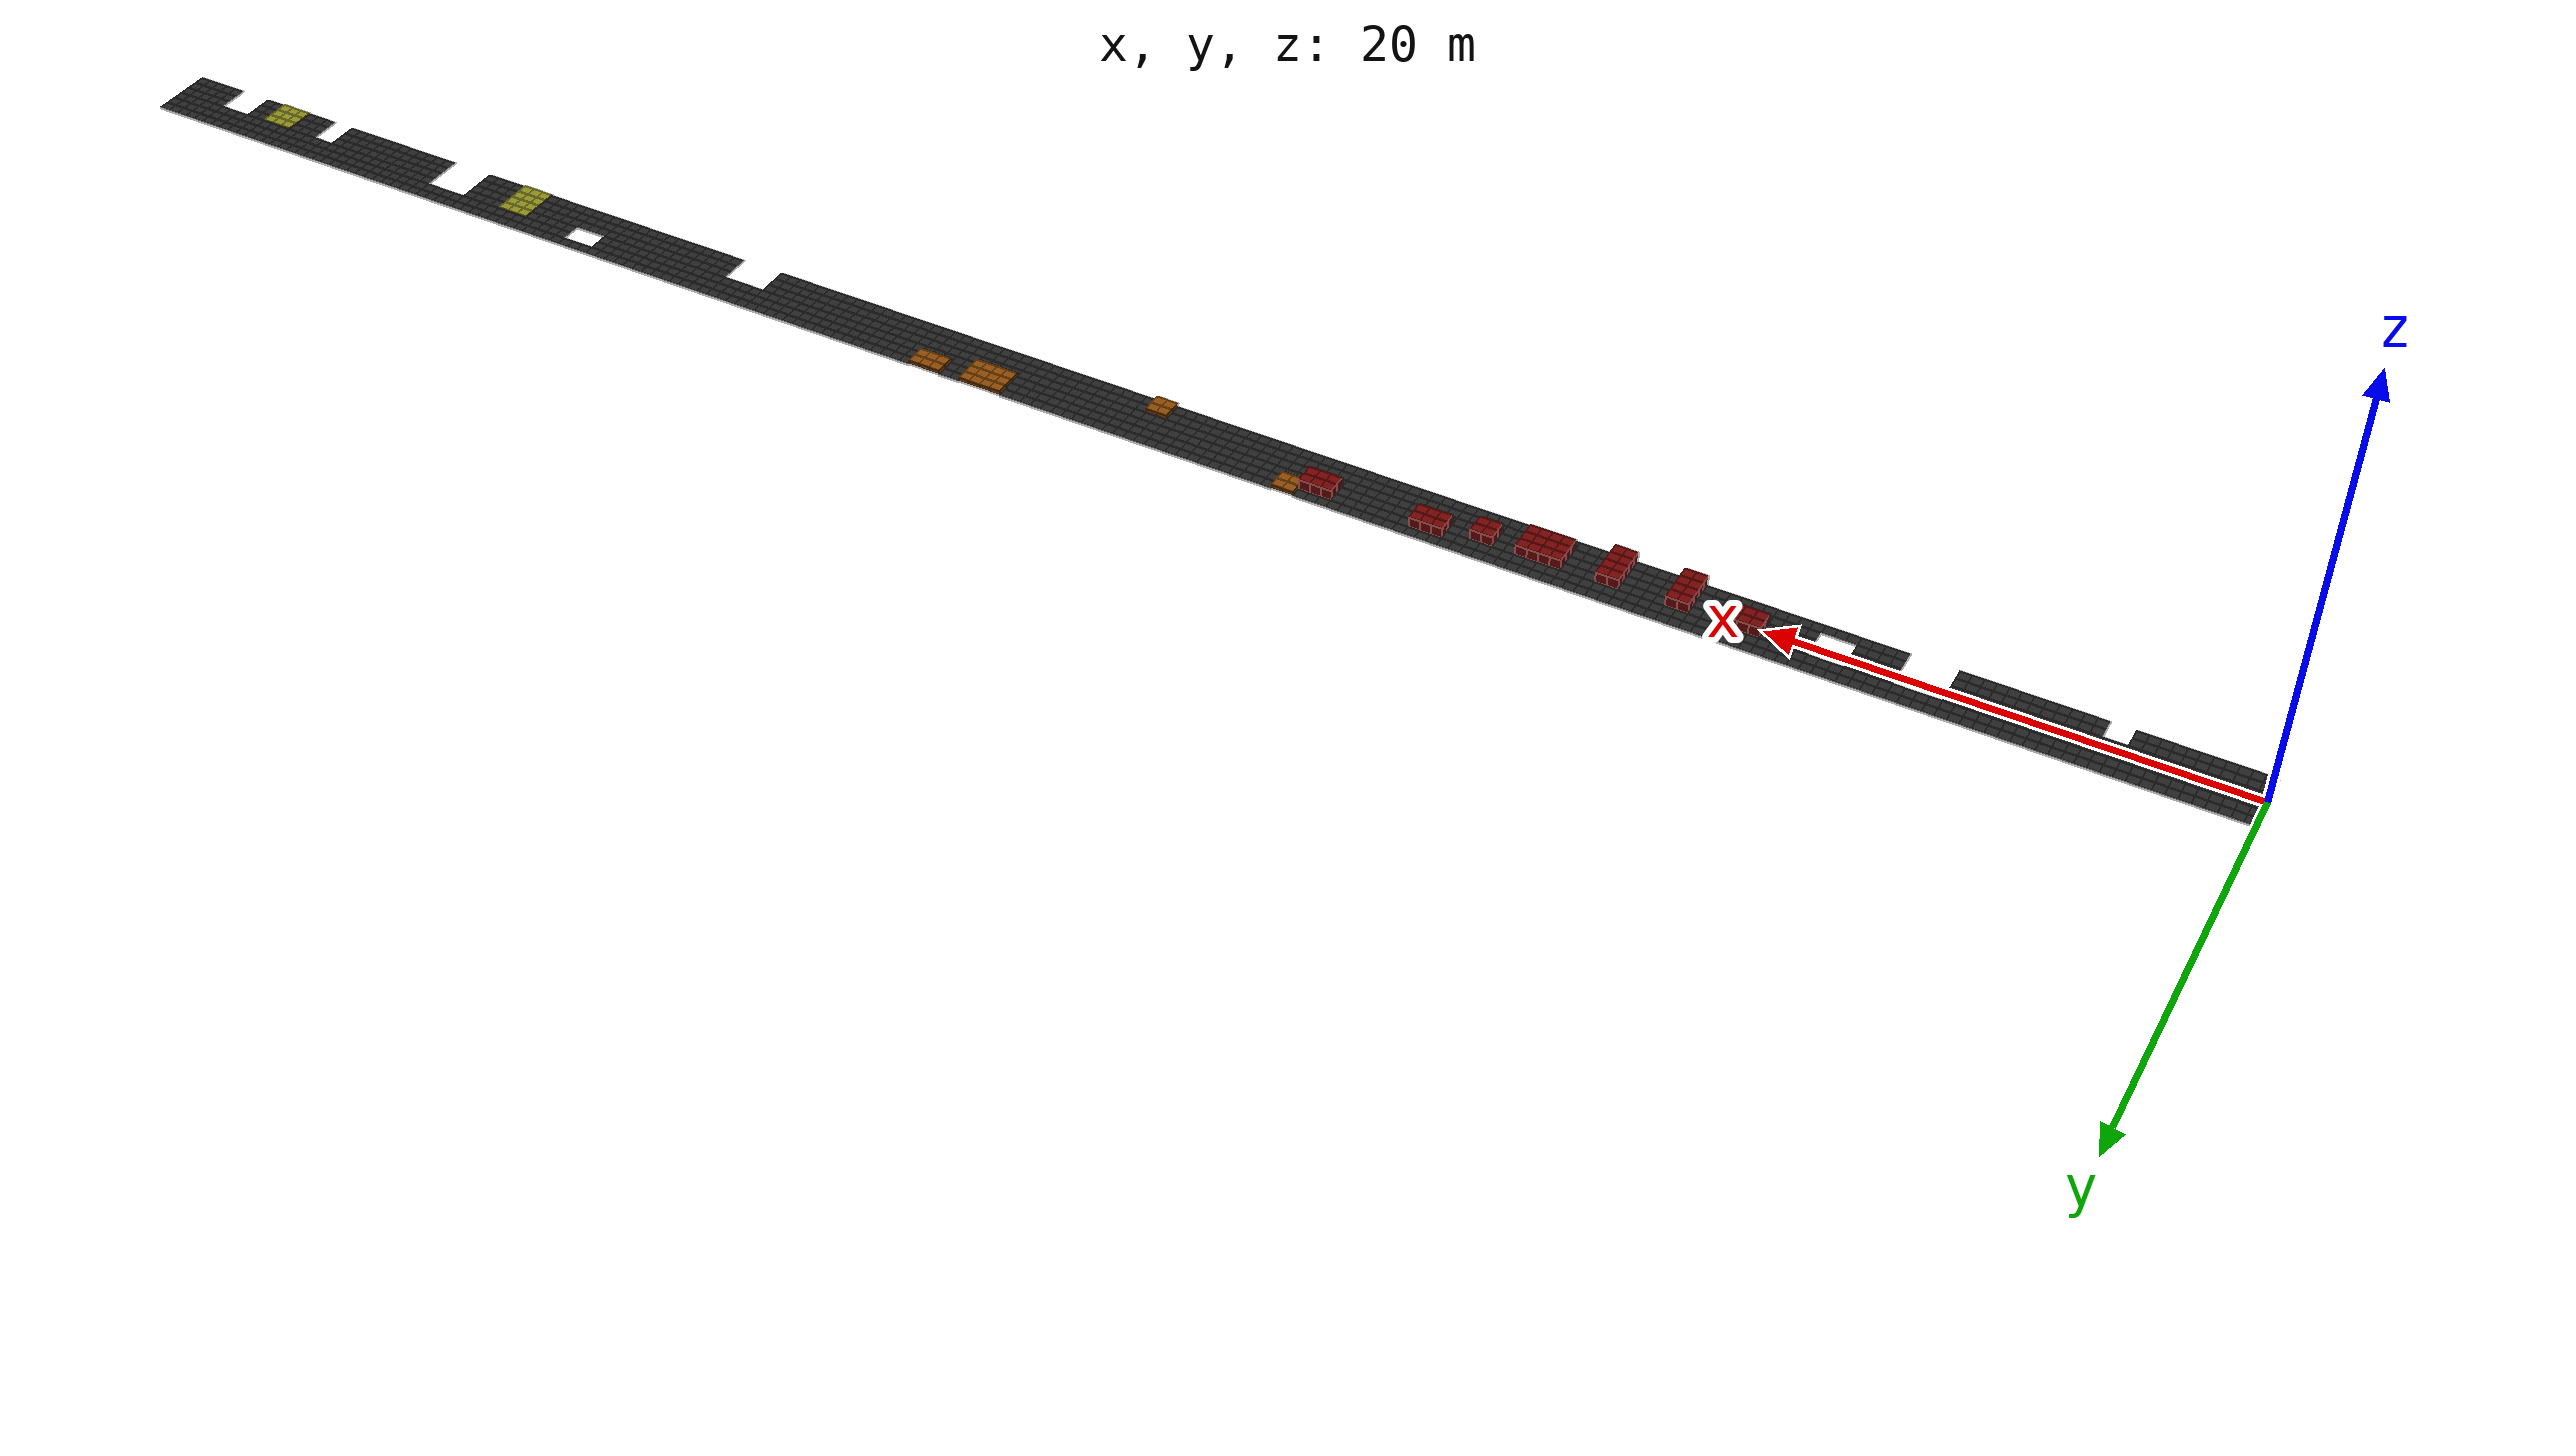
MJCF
<?xml version='1.0' encoding='utf-8'?>
<mujoco model="corridor_3x100">
  <compiler angle="degree" autolimits="true" />
  <option timestep="0.005" gravity="0 0 -9.81" />
  <size njmax="4000" nconmax="1000" />
  <asset>
    <texture name="tex_grid" type="2d" builtin="checker" rgb1="0.1 0.1 0.1" rgb2="0.15 0.15 0.15" width="300" height="300" mark="edge" markrgb="0.8 0.8 0.8" />
    <texture name="tex_wall" type="2d" builtin="checker" rgb1="0.5 0.5 0.5" rgb2="0.55 0.55 0.55" width="300" height="300" />
    <material name="mat_floor" texture="tex_grid" texrepeat="2 2" specular="0.1" shininess="0.1" />
    <material name="mat_bump_small" texture="tex_wall" rgba="1 1 0.2 1" specular="0.5" shininess="0.5" />
    <material name="mat_bump_medium" texture="tex_wall" rgba="1 0.5 0 1" specular="0.5" shininess="0.5" />
    <material name="mat_bump_large" texture="tex_wall" rgba="0.8 0 0 1" specular="0.5" shininess="0.5" />
  </asset>
  <worldbody>
    <light name="key_light" pos="4 4 4" dir="-1 -1 -1" directional="true" diffuse="1.1 1.1 1.1" specular="0.4 0.4 0.4" castshadow="true" />
    <light name="fill_light" pos="-6 4 2" dir="1 -0.5 -1" directional="true" ambient="0.4 0.4 0.4" diffuse="0.6 0.6 0.6" specular="0.2 0.2 0.2" castshadow="false" />

    <geom type="box" material="mat_floor" size="0.250 0.250 0.025" pos="0.250 -1.250 0.025" name="flat_0" />
    <geom type="box" material="mat_floor" size="0.250 0.250 0.025" pos="0.250 -0.750 0.025" name="flat_1" />
    <geom type="box" material="mat_floor" size="0.250 0.250 0.025" pos="0.250 -0.250 0.025" name="flat_2" />
    <geom type="box" material="mat_floor" size="0.250 0.250 0.025" pos="0.250 0.250 0.025" name="flat_3" />
    <geom type="box" material="mat_floor" size="0.250 0.250 0.025" pos="0.250 0.750 0.025" name="flat_4" />
    <geom type="box" material="mat_floor" size="0.250 0.250 0.025" pos="0.250 1.250 0.025" name="flat_5" />
    <geom type="box" material="mat_floor" size="0.250 0.250 0.025" pos="0.750 -1.250 0.025" name="flat_6" />
    <geom type="box" material="mat_floor" size="0.250 0.250 0.025" pos="0.750 -0.750 0.025" name="flat_7" />
    <geom type="box" material="mat_floor" size="0.250 0.250 0.025" pos="0.750 -0.250 0.025" name="flat_8" />
    <geom type="box" material="mat_floor" size="0.250 0.250 0.025" pos="0.750 0.250 0.025" name="flat_9" />
    <geom type="box" material="mat_floor" size="0.250 0.250 0.025" pos="0.750 0.750 0.025" name="flat_10" />
    <geom type="box" material="mat_floor" size="0.250 0.250 0.025" pos="0.750 1.250 0.025" name="flat_11" />
    <geom type="box" material="mat_floor" size="0.250 0.250 0.025" pos="1.250 -1.250 0.025" name="flat_12" />
    <geom type="box" material="mat_floor" size="0.250 0.250 0.025" pos="1.250 -0.750 0.025" name="flat_13" />
    <geom type="box" material="mat_floor" size="0.250 0.250 0.025" pos="1.250 -0.250 0.025" name="flat_14" />
    <geom type="box" material="mat_floor" size="0.250 0.250 0.025" pos="1.250 0.250 0.025" name="flat_15" />
    <geom type="box" material="mat_floor" size="0.250 0.250 0.025" pos="1.250 0.750 0.025" name="flat_16" />
    <geom type="box" material="mat_floor" size="0.250 0.250 0.025" pos="1.250 1.250 0.025" name="flat_17" />
    <geom type="box" material="mat_floor" size="0.250 0.250 0.025" pos="1.750 -1.250 0.025" name="flat_18" />
    <geom type="box" material="mat_floor" size="0.250 0.250 0.025" pos="1.750 -0.750 0.025" name="flat_19" />
    <geom type="box" material="mat_floor" size="0.250 0.250 0.025" pos="1.750 -0.250 0.025" name="flat_20" />
    <geom type="box" material="mat_floor" size="0.250 0.250 0.025" pos="1.750 0.250 0.025" name="flat_21" />
    <geom type="box" material="mat_floor" size="0.250 0.250 0.025" pos="1.750 0.750 0.025" name="flat_22" />
    <geom type="box" material="mat_floor" size="0.250 0.250 0.025" pos="1.750 1.250 0.025" name="flat_23" />
    <geom type="box" material="mat_floor" size="0.250 0.250 0.025" pos="2.250 -1.250 0.025" name="flat_24" />
    <geom type="box" material="mat_floor" size="0.250 0.250 0.025" pos="2.250 -0.750 0.025" name="flat_25" />
    <geom type="box" material="mat_floor" size="0.250 0.250 0.025" pos="2.250 -0.250 0.025" name="flat_26" />
    <geom type="box" material="mat_floor" size="0.250 0.250 0.025" pos="2.250 0.250 0.025" name="flat_27" />
    <geom type="box" material="mat_floor" size="0.250 0.250 0.025" pos="2.250 0.750 0.025" name="flat_28" />
    <geom type="box" material="mat_floor" size="0.250 0.250 0.025" pos="2.250 1.250 0.025" name="flat_29" />
    <geom type="box" material="mat_floor" size="0.250 0.250 0.025" pos="2.750 -1.250 0.025" name="flat_30" />
    <geom type="box" material="mat_floor" size="0.250 0.250 0.025" pos="2.750 -0.750 0.025" name="flat_31" />
    <geom type="box" material="mat_floor" size="0.250 0.250 0.025" pos="2.750 -0.250 0.025" name="flat_32" />
    <geom type="box" material="mat_floor" size="0.250 0.250 0.025" pos="2.750 0.250 0.025" name="flat_33" />
    <geom type="box" material="mat_floor" size="0.250 0.250 0.025" pos="2.750 0.750 0.025" name="flat_34" />
    <geom type="box" material="mat_floor" size="0.250 0.250 0.025" pos="2.750 1.250 0.025" name="flat_35" />
    <geom type="box" material="mat_floor" size="0.250 0.250 0.025" pos="3.250 -1.250 0.025" name="flat_36" />
    <geom type="box" material="mat_floor" size="0.250 0.250 0.025" pos="3.250 -0.750 0.025" name="flat_37" />
    <geom type="box" material="mat_floor" size="0.250 0.250 0.025" pos="3.250 -0.250 0.025" name="flat_38" />
    <geom type="box" material="mat_floor" size="0.250 0.250 0.025" pos="3.250 0.250 0.025" name="flat_39" />
    <geom type="box" material="mat_floor" size="0.250 0.250 0.025" pos="3.250 0.750 0.025" name="flat_40" />
    <geom type="box" material="mat_floor" size="0.250 0.250 0.025" pos="3.250 1.250 0.025" name="flat_41" />
    <geom type="box" material="mat_floor" size="0.250 0.250 0.025" pos="3.750 -1.250 0.025" name="flat_42" />
    <geom type="box" material="mat_floor" size="0.250 0.250 0.025" pos="3.750 -0.750 0.025" name="flat_43" />
    <geom type="box" material="mat_floor" size="0.250 0.250 0.025" pos="3.750 -0.250 0.025" name="flat_44" />
    <geom type="box" material="mat_floor" size="0.250 0.250 0.025" pos="3.750 0.250 0.025" name="flat_45" />
    <geom type="box" material="mat_floor" size="0.250 0.250 0.025" pos="3.750 0.750 0.025" name="flat_46" />
    <geom type="box" material="mat_floor" size="0.250 0.250 0.025" pos="3.750 1.250 0.025" name="flat_47" />
    <geom type="box" material="mat_floor" size="0.250 0.250 0.025" pos="4.250 -1.250 0.025" name="flat_48" />
    <geom type="box" material="mat_floor" size="0.250 0.250 0.025" pos="4.250 -0.750 0.025" name="flat_49" />
    <geom type="box" material="mat_floor" size="0.250 0.250 0.025" pos="4.250 -0.250 0.025" name="flat_50" />
    <geom type="box" material="mat_floor" size="0.250 0.250 0.025" pos="4.250 0.250 0.025" name="flat_51" />
    <geom type="box" material="mat_floor" size="0.250 0.250 0.025" pos="4.250 0.750 0.025" name="flat_52" />
    <geom type="box" material="mat_floor" size="0.250 0.250 0.025" pos="4.250 1.250 0.025" name="flat_53" />
    <geom type="box" material="mat_floor" size="0.250 0.250 0.025" pos="4.750 -1.250 0.025" name="flat_54" />
    <geom type="box" material="mat_floor" size="0.250 0.250 0.025" pos="4.750 -0.750 0.025" name="flat_55" />
    <geom type="box" material="mat_floor" size="0.250 0.250 0.025" pos="4.750 -0.250 0.025" name="flat_56" />
    <geom type="box" material="mat_floor" size="0.250 0.250 0.025" pos="4.750 0.250 0.025" name="flat_57" />
    <geom type="box" material="mat_floor" size="0.250 0.250 0.025" pos="4.750 0.750 0.025" name="flat_58" />
    <geom type="box" material="mat_floor" size="0.250 0.250 0.025" pos="4.750 1.250 0.025" name="flat_59" />
    <geom type="box" material="mat_floor" size="0.250 0.250 0.025" pos="5.250 -1.250 0.025" name="flat_60" />
    <geom type="box" material="mat_floor" size="0.250 0.250 0.025" pos="5.250 -0.750 0.025" name="flat_61" />
    <geom type="box" material="mat_floor" size="0.250 0.250 0.025" pos="5.250 -0.250 0.025" name="flat_62" />
    <geom type="box" material="mat_floor" size="0.250 0.250 0.025" pos="5.250 0.250 0.025" name="flat_63" />
    <geom type="box" material="mat_floor" size="0.250 0.250 0.025" pos="5.250 0.750 0.025" name="flat_64" />
    <geom type="box" material="mat_floor" size="0.250 0.250 0.025" pos="5.250 1.250 0.025" name="flat_65" />
    <geom type="box" material="mat_floor" size="0.250 0.250 0.025" pos="5.750 -0.250 0.025" name="flat_66" />
    <geom type="box" material="mat_floor" size="0.250 0.250 0.025" pos="5.750 0.250 0.025" name="flat_67" />
    <geom type="box" material="mat_floor" size="0.250 0.250 0.025" pos="5.750 0.750 0.025" name="flat_68" />
    <geom type="box" material="mat_floor" size="0.250 0.250 0.025" pos="5.750 1.250 0.025" name="flat_69" />
    <geom type="box" material="mat_floor" size="0.250 0.250 0.025" pos="6.250 -0.250 0.025" name="flat_70" />
    <geom type="box" material="mat_floor" size="0.250 0.250 0.025" pos="6.250 0.250 0.025" name="flat_71" />
    <geom type="box" material="mat_floor" size="0.250 0.250 0.025" pos="6.250 0.750 0.025" name="flat_72" />
    <geom type="box" material="mat_floor" size="0.250 0.250 0.025" pos="6.250 1.250 0.025" name="flat_73" />
    <geom type="box" material="mat_floor" size="0.250 0.250 0.025" pos="6.750 -1.250 0.025" name="flat_74" />
    <geom type="box" material="mat_floor" size="0.250 0.250 0.025" pos="6.750 -0.750 0.025" name="flat_75" />
    <geom type="box" material="mat_floor" size="0.250 0.250 0.025" pos="6.750 -0.250 0.025" name="flat_76" />
    <geom type="box" material="mat_floor" size="0.250 0.250 0.025" pos="6.750 0.250 0.025" name="flat_77" />
    <geom type="box" material="mat_floor" size="0.250 0.250 0.025" pos="6.750 0.750 0.025" name="flat_78" />
    <geom type="box" material="mat_floor" size="0.250 0.250 0.025" pos="6.750 1.250 0.025" name="flat_79" />
    <geom type="box" material="mat_floor" size="0.250 0.250 0.025" pos="7.250 -1.250 0.025" name="flat_80" />
    <geom type="box" material="mat_floor" size="0.250 0.250 0.025" pos="7.250 -0.750 0.025" name="flat_81" />
    <geom type="box" material="mat_floor" size="0.250 0.250 0.025" pos="7.250 -0.250 0.025" name="flat_82" />
    <geom type="box" material="mat_floor" size="0.250 0.250 0.025" pos="7.250 0.250 0.025" name="flat_83" />
    <geom type="box" material="mat_floor" size="0.250 0.250 0.025" pos="7.250 0.750 0.025" name="flat_84" />
    <geom type="box" material="mat_floor" size="0.250 0.250 0.025" pos="7.250 1.250 0.025" name="flat_85" />
    <geom type="box" material="mat_floor" size="0.250 0.250 0.025" pos="7.750 -1.250 0.025" name="flat_86" />
    <geom type="box" material="mat_floor" size="0.250 0.250 0.025" pos="7.750 -0.750 0.025" name="flat_87" />
    <geom type="box" material="mat_floor" size="0.250 0.250 0.025" pos="7.750 -0.250 0.025" name="flat_88" />
    <geom type="box" material="mat_floor" size="0.250 0.250 0.025" pos="7.750 0.250 0.025" name="flat_89" />
    <geom type="box" material="mat_floor" size="0.250 0.250 0.025" pos="7.750 0.750 0.025" name="flat_90" />
    <geom type="box" material="mat_floor" size="0.250 0.250 0.025" pos="7.750 1.250 0.025" name="flat_91" />
    <geom type="box" material="mat_floor" size="0.250 0.250 0.025" pos="8.250 -1.250 0.025" name="flat_92" />
    <geom type="box" material="mat_floor" size="0.250 0.250 0.025" pos="8.250 -0.750 0.025" name="flat_93" />
    <geom type="box" material="mat_floor" size="0.250 0.250 0.025" pos="8.250 -0.250 0.025" name="flat_94" />
    <geom type="box" material="mat_floor" size="0.250 0.250 0.025" pos="8.250 0.250 0.025" name="flat_95" />
    <geom type="box" material="mat_floor" size="0.250 0.250 0.025" pos="8.250 0.750 0.025" name="flat_96" />
    <geom type="box" material="mat_floor" size="0.250 0.250 0.025" pos="8.250 1.250 0.025" name="flat_97" />
    <geom type="box" material="mat_floor" size="0.250 0.250 0.025" pos="8.750 -1.250 0.025" name="flat_98" />
    <geom type="box" material="mat_floor" size="0.250 0.250 0.025" pos="8.750 -0.750 0.025" name="flat_99" />
    <geom type="box" material="mat_floor" size="0.250 0.250 0.025" pos="8.750 -0.250 0.025" name="flat_100" />
    <geom type="box" material="mat_floor" size="0.250 0.250 0.025" pos="8.750 0.250 0.025" name="flat_101" />
    <geom type="box" material="mat_floor" size="0.250 0.250 0.025" pos="8.750 0.750 0.025" name="flat_102" />
    <geom type="box" material="mat_floor" size="0.250 0.250 0.025" pos="8.750 1.250 0.025" name="flat_103" />
    <geom type="box" material="mat_floor" size="0.250 0.250 0.025" pos="9.250 -1.250 0.025" name="flat_104" />
    <geom type="box" material="mat_floor" size="0.250 0.250 0.025" pos="9.250 -0.750 0.025" name="flat_105" />
    <geom type="box" material="mat_floor" size="0.250 0.250 0.025" pos="9.250 -0.250 0.025" name="flat_106" />
    <geom type="box" material="mat_floor" size="0.250 0.250 0.025" pos="9.250 0.250 0.025" name="flat_107" />
    <geom type="box" material="mat_floor" size="0.250 0.250 0.025" pos="9.250 0.750 0.025" name="flat_108" />
    <geom type="box" material="mat_floor" size="0.250 0.250 0.025" pos="9.250 1.250 0.025" name="flat_109" />
    <geom type="box" material="mat_floor" size="0.250 0.250 0.025" pos="9.750 -1.250 0.025" name="flat_110" />
    <geom type="box" material="mat_floor" size="0.250 0.250 0.025" pos="9.750 -0.750 0.025" name="flat_111" />
    <geom type="box" material="mat_floor" size="0.250 0.250 0.025" pos="9.750 -0.250 0.025" name="flat_112" />
    <geom type="box" material="mat_floor" size="0.250 0.250 0.025" pos="9.750 0.250 0.025" name="flat_113" />
    <geom type="box" material="mat_floor" size="0.250 0.250 0.025" pos="9.750 0.750 0.025" name="flat_114" />
    <geom type="box" material="mat_floor" size="0.250 0.250 0.025" pos="9.750 1.250 0.025" name="flat_115" />
    <geom type="box" material="mat_floor" size="0.250 0.250 0.025" pos="10.250 -1.250 0.025" name="flat_116" />
    <geom type="box" material="mat_floor" size="0.250 0.250 0.025" pos="10.250 -0.750 0.025" name="flat_117" />
    <geom type="box" material="mat_floor" size="0.250 0.250 0.025" pos="10.250 -0.250 0.025" name="flat_118" />
    <geom type="box" material="mat_floor" size="0.250 0.250 0.025" pos="10.250 0.250 0.025" name="flat_119" />
    <geom type="box" material="mat_floor" size="0.250 0.250 0.025" pos="10.250 0.750 0.025" name="flat_120" />
    <geom type="box" material="mat_floor" size="0.250 0.250 0.025" pos="10.250 1.250 0.025" name="flat_121" />
    <geom type="box" material="mat_floor" size="0.250 0.250 0.025" pos="10.750 -1.250 0.025" name="flat_122" />
    <geom type="box" material="mat_floor" size="0.250 0.250 0.025" pos="10.750 -0.750 0.025" name="flat_123" />
    <geom type="box" material="mat_floor" size="0.250 0.250 0.025" pos="10.750 -0.250 0.025" name="flat_124" />
    <geom type="box" material="mat_floor" size="0.250 0.250 0.025" pos="10.750 0.250 0.025" name="flat_125" />
    <geom type="box" material="mat_floor" size="0.250 0.250 0.025" pos="10.750 0.750 0.025" name="flat_126" />
    <geom type="box" material="mat_floor" size="0.250 0.250 0.025" pos="10.750 1.250 0.025" name="flat_127" />
    <geom type="box" material="mat_floor" size="0.250 0.250 0.025" pos="11.250 -1.250 0.025" name="flat_128" />
    <geom type="box" material="mat_floor" size="0.250 0.250 0.025" pos="11.250 -0.750 0.025" name="flat_129" />
    <geom type="box" material="mat_floor" size="0.250 0.250 0.025" pos="11.250 -0.250 0.025" name="flat_130" />
    <geom type="box" material="mat_floor" size="0.250 0.250 0.025" pos="11.250 0.250 0.025" name="flat_131" />
    <geom type="box" material="mat_floor" size="0.250 0.250 0.025" pos="11.250 0.750 0.025" name="flat_132" />
    <geom type="box" material="mat_floor" size="0.250 0.250 0.025" pos="11.250 1.250 0.025" name="flat_133" />
    <geom type="box" material="mat_floor" size="0.250 0.250 0.025" pos="11.750 -1.250 0.025" name="flat_134" />
    <geom type="box" material="mat_floor" size="0.250 0.250 0.025" pos="11.750 -0.750 0.025" name="flat_135" />
    <geom type="box" material="mat_floor" size="0.250 0.250 0.025" pos="11.750 -0.250 0.025" name="flat_136" />
    <geom type="box" material="mat_floor" size="0.250 0.250 0.025" pos="11.750 0.250 0.025" name="flat_137" />
    <geom type="box" material="mat_floor" size="0.250 0.250 0.025" pos="11.750 0.750 0.025" name="flat_138" />
    <geom type="box" material="mat_floor" size="0.250 0.250 0.025" pos="11.750 1.250 0.025" name="flat_139" />
    <geom type="box" material="mat_floor" size="0.250 0.250 0.025" pos="12.250 -1.250 0.025" name="flat_140" />
    <geom type="box" material="mat_floor" size="0.250 0.250 0.025" pos="12.250 -0.750 0.025" name="flat_141" />
    <geom type="box" material="mat_floor" size="0.250 0.250 0.025" pos="12.250 -0.250 0.025" name="flat_142" />
    <geom type="box" material="mat_floor" size="0.250 0.250 0.025" pos="12.250 0.250 0.025" name="flat_143" />
    <geom type="box" material="mat_floor" size="0.250 0.250 0.025" pos="12.250 0.750 0.025" name="flat_144" />
    <geom type="box" material="mat_floor" size="0.250 0.250 0.025" pos="12.250 1.250 0.025" name="flat_145" />
    <geom type="box" material="mat_floor" size="0.250 0.250 0.025" pos="12.750 0.750 0.025" name="flat_146" />
    <geom type="box" material="mat_floor" size="0.250 0.250 0.025" pos="12.750 1.250 0.025" name="flat_147" />
    <geom type="box" material="mat_floor" size="0.250 0.250 0.025" pos="13.250 0.750 0.025" name="flat_148" />
    <geom type="box" material="mat_floor" size="0.250 0.250 0.025" pos="13.250 1.250 0.025" name="flat_149" />
    <geom type="box" material="mat_floor" size="0.250 0.250 0.025" pos="13.750 0.750 0.025" name="flat_150" />
    <geom type="box" material="mat_floor" size="0.250 0.250 0.025" pos="13.750 1.250 0.025" name="flat_151" />
    <geom type="box" material="mat_floor" size="0.250 0.250 0.025" pos="14.250 0.750 0.025" name="flat_152" />
    <geom type="box" material="mat_floor" size="0.250 0.250 0.025" pos="14.250 1.250 0.025" name="flat_153" />
    <geom type="box" material="mat_floor" size="0.250 0.250 0.025" pos="14.750 -1.250 0.025" name="flat_154" />
    <geom type="box" material="mat_floor" size="0.250 0.250 0.025" pos="14.750 -0.750 0.025" name="flat_155" />
    <geom type="box" material="mat_floor" size="0.250 0.250 0.025" pos="14.750 -0.250 0.025" name="flat_156" />
    <geom type="box" material="mat_floor" size="0.250 0.250 0.025" pos="14.750 0.250 0.025" name="flat_157" />
    <geom type="box" material="mat_floor" size="0.250 0.250 0.025" pos="14.750 0.750 0.025" name="flat_158" />
    <geom type="box" material="mat_floor" size="0.250 0.250 0.025" pos="14.750 1.250 0.025" name="flat_159" />
    <geom type="box" material="mat_floor" size="0.250 0.250 0.025" pos="15.250 -1.250 0.025" name="flat_160" />
    <geom type="box" material="mat_floor" size="0.250 0.250 0.025" pos="15.250 -0.750 0.025" name="flat_161" />
    <geom type="box" material="mat_floor" size="0.250 0.250 0.025" pos="15.250 -0.250 0.025" name="flat_162" />
    <geom type="box" material="mat_floor" size="0.250 0.250 0.025" pos="15.250 0.250 0.025" name="flat_163" />
    <geom type="box" material="mat_floor" size="0.250 0.250 0.025" pos="15.250 0.750 0.025" name="flat_164" />
    <geom type="box" material="mat_floor" size="0.250 0.250 0.025" pos="15.250 1.250 0.025" name="flat_165" />
    <geom type="box" material="mat_floor" size="0.250 0.250 0.025" pos="15.750 -1.250 0.025" name="flat_166" />
    <geom type="box" material="mat_floor" size="0.250 0.250 0.025" pos="15.750 -0.750 0.025" name="flat_167" />
    <geom type="box" material="mat_floor" size="0.250 0.250 0.025" pos="15.750 -0.250 0.025" name="flat_168" />
    <geom type="box" material="mat_floor" size="0.250 0.250 0.025" pos="15.750 0.250 0.025" name="flat_169" />
    <geom type="box" material="mat_floor" size="0.250 0.250 0.025" pos="15.750 0.750 0.025" name="flat_170" />
    <geom type="box" material="mat_floor" size="0.250 0.250 0.025" pos="15.750 1.250 0.025" name="flat_171" />
    <geom type="box" material="mat_floor" size="0.250 0.250 0.025" pos="16.250 -1.250 0.025" name="flat_172" />
    <geom type="box" material="mat_floor" size="0.250 0.250 0.025" pos="16.250 -0.750 0.025" name="flat_173" />
    <geom type="box" material="mat_floor" size="0.250 0.250 0.025" pos="16.250 -0.250 0.025" name="flat_174" />
    <geom type="box" material="mat_floor" size="0.250 0.250 0.025" pos="16.250 0.250 0.025" name="flat_175" />
    <geom type="box" material="mat_floor" size="0.250 0.250 0.025" pos="16.250 0.750 0.025" name="flat_176" />
    <geom type="box" material="mat_floor" size="0.250 0.250 0.025" pos="16.250 1.250 0.025" name="flat_177" />
    <geom type="box" material="mat_floor" size="0.250 0.250 0.025" pos="16.750 -1.250 0.025" name="flat_178" />
    <geom type="box" material="mat_floor" size="0.250 0.250 0.025" pos="16.750 0.750 0.025" name="flat_179" />
    <geom type="box" material="mat_floor" size="0.250 0.250 0.025" pos="16.750 1.250 0.025" name="flat_180" />
    <geom type="box" material="mat_floor" size="0.250 0.250 0.025" pos="17.250 -1.250 0.025" name="flat_181" />
    <geom type="box" material="mat_floor" size="0.250 0.250 0.025" pos="17.250 0.750 0.025" name="flat_182" />
    <geom type="box" material="mat_floor" size="0.250 0.250 0.025" pos="17.250 1.250 0.025" name="flat_183" />
    <geom type="box" material="mat_floor" size="0.250 0.250 0.025" pos="17.750 -1.250 0.025" name="flat_184" />
    <geom type="box" material="mat_floor" size="0.250 0.250 0.025" pos="17.750 0.750 0.025" name="flat_185" />
    <geom type="box" material="mat_floor" size="0.250 0.250 0.025" pos="17.750 1.250 0.025" name="flat_186" />
    <geom type="box" material="mat_floor" size="0.250 0.250 0.025" pos="18.250 -1.250 0.025" name="flat_187" />
    <geom type="box" material="mat_floor" size="0.250 0.250 0.025" pos="18.250 -0.750 0.025" name="flat_188" />
    <geom type="box" material="mat_floor" size="0.250 0.250 0.025" pos="18.250 -0.250 0.025" name="flat_189" />
    <geom type="box" material="mat_floor" size="0.250 0.250 0.025" pos="18.250 0.250 0.025" name="flat_190" />
    <geom type="box" material="mat_floor" size="0.250 0.250 0.025" pos="18.250 0.750 0.025" name="flat_191" />
    <geom type="box" material="mat_floor" size="0.250 0.250 0.025" pos="18.250 1.250 0.025" name="flat_192" />
    <geom type="box" material="mat_floor" size="0.250 0.250 0.025" pos="18.750 -1.250 0.025" name="flat_193" />
    <geom type="box" material="mat_floor" size="0.250 0.250 0.025" pos="18.750 -0.750 0.025" name="flat_194" />
    <geom type="box" material="mat_floor" size="0.250 0.250 0.025" pos="18.750 -0.250 0.025" name="flat_195" />
    <geom type="box" material="mat_floor" size="0.250 0.250 0.025" pos="18.750 0.250 0.025" name="flat_196" />
    <geom type="box" material="mat_floor" size="0.250 0.250 0.025" pos="18.750 0.750 0.025" name="flat_197" />
    <geom type="box" material="mat_floor" size="0.250 0.250 0.025" pos="18.750 1.250 0.025" name="flat_198" />
    <geom type="box" material="mat_floor" size="0.250 0.250 0.025" pos="19.250 -1.250 0.025" name="flat_199" />
    <geom type="box" material="mat_floor" size="0.250 0.250 0.025" pos="19.250 -0.750 0.025" name="flat_200" />
    <geom type="box" material="mat_floor" size="0.250 0.250 0.025" pos="19.250 -0.250 0.025" name="flat_201" />
    <geom type="box" material="mat_floor" size="0.250 0.250 0.025" pos="19.250 0.250 0.025" name="flat_202" />
    <geom type="box" material="mat_floor" size="0.250 0.250 0.025" pos="19.250 0.750 0.025" name="flat_203" />
    <geom type="box" material="mat_floor" size="0.250 0.250 0.025" pos="19.250 1.250 0.025" name="flat_204" />
    <geom type="box" material="mat_floor" size="0.250 0.250 0.025" pos="19.750 -1.250 0.025" name="flat_205" />
    <geom type="box" material="mat_floor" size="0.250 0.250 0.025" pos="19.750 -0.750 0.025" name="flat_206" />
    <geom type="box" material="mat_floor" size="0.250 0.250 0.025" pos="19.750 -0.250 0.025" name="flat_207" />
    <geom type="box" material="mat_floor" size="0.250 0.250 0.025" pos="19.750 0.250 0.025" name="flat_208" />
    <geom type="box" material="mat_floor" size="0.250 0.250 0.025" pos="19.750 0.750 0.025" name="flat_209" />
    <geom type="box" material="mat_floor" size="0.250 0.250 0.025" pos="19.750 1.250 0.025" name="flat_210" />
    <geom type="box" material="mat_floor" size="0.250 0.250 0.025" pos="20.250 -1.250 0.025" name="flat_211" />
    <geom type="box" material="mat_floor" size="0.250 0.250 0.025" pos="20.250 -0.750 0.025" name="flat_212" />
    <geom type="box" material="mat_bump_large" size="0.250 0.250 0.250" pos="20.250 -0.250 0.300" name="bump_0" />
    <geom type="box" material="mat_bump_large" size="0.250 0.250 0.250" pos="20.250 0.250 0.300" name="bump_1" />
    <geom type="box" material="mat_floor" size="0.250 0.250 0.025" pos="20.250 0.750 0.025" name="flat_213" />
    <geom type="box" material="mat_floor" size="0.250 0.250 0.025" pos="20.250 1.250 0.025" name="flat_214" />
    <geom type="box" material="mat_floor" size="0.250 0.250 0.025" pos="20.750 -1.250 0.025" name="flat_215" />
    <geom type="box" material="mat_floor" size="0.250 0.250 0.025" pos="20.750 -0.750 0.025" name="flat_216" />
    <geom type="box" material="mat_bump_large" size="0.250 0.250 0.250" pos="20.750 -0.250 0.300" name="bump_2" />
    <geom type="box" material="mat_bump_large" size="0.250 0.250 0.250" pos="20.750 0.250 0.300" name="bump_3" />
    <geom type="box" material="mat_floor" size="0.250 0.250 0.025" pos="20.750 0.750 0.025" name="flat_217" />
    <geom type="box" material="mat_floor" size="0.250 0.250 0.025" pos="20.750 1.250 0.025" name="flat_218" />
    <geom type="box" material="mat_floor" size="0.250 0.250 0.025" pos="21.250 -1.250 0.025" name="flat_219" />
    <geom type="box" material="mat_floor" size="0.250 0.250 0.025" pos="21.250 -0.750 0.025" name="flat_220" />
    <geom type="box" material="mat_bump_large" size="0.250 0.250 0.250" pos="21.250 -0.250 0.300" name="bump_4" />
    <geom type="box" material="mat_bump_large" size="0.250 0.250 0.250" pos="21.250 0.250 0.300" name="bump_5" />
    <geom type="box" material="mat_floor" size="0.250 0.250 0.025" pos="21.250 0.750 0.025" name="flat_221" />
    <geom type="box" material="mat_floor" size="0.250 0.250 0.025" pos="21.250 1.250 0.025" name="flat_222" />
    <geom type="box" material="mat_floor" size="0.250 0.250 0.025" pos="21.750 -1.250 0.025" name="flat_223" />
    <geom type="box" material="mat_floor" size="0.250 0.250 0.025" pos="21.750 -0.750 0.025" name="flat_224" />
    <geom type="box" material="mat_floor" size="0.250 0.250 0.025" pos="21.750 -0.250 0.025" name="flat_225" />
    <geom type="box" material="mat_floor" size="0.250 0.250 0.025" pos="21.750 0.250 0.025" name="flat_226" />
    <geom type="box" material="mat_floor" size="0.250 0.250 0.025" pos="21.750 0.750 0.025" name="flat_227" />
    <geom type="box" material="mat_floor" size="0.250 0.250 0.025" pos="21.750 1.250 0.025" name="flat_228" />
    <geom type="box" material="mat_floor" size="0.250 0.250 0.025" pos="22.250 -1.250 0.025" name="flat_229" />
    <geom type="box" material="mat_floor" size="0.250 0.250 0.025" pos="22.250 -0.750 0.025" name="flat_230" />
    <geom type="box" material="mat_floor" size="0.250 0.250 0.025" pos="22.250 -0.250 0.025" name="flat_231" />
    <geom type="box" material="mat_floor" size="0.250 0.250 0.025" pos="22.250 0.250 0.025" name="flat_232" />
    <geom type="box" material="mat_floor" size="0.250 0.250 0.025" pos="22.250 0.750 0.025" name="flat_233" />
    <geom type="box" material="mat_floor" size="0.250 0.250 0.025" pos="22.250 1.250 0.025" name="flat_234" />
    <geom type="box" material="mat_floor" size="0.250 0.250 0.025" pos="22.750 -1.250 0.025" name="flat_235" />
    <geom type="box" material="mat_floor" size="0.250 0.250 0.025" pos="22.750 -0.750 0.025" name="flat_236" />
    <geom type="box" material="mat_floor" size="0.250 0.250 0.025" pos="22.750 -0.250 0.025" name="flat_237" />
    <geom type="box" material="mat_floor" size="0.250 0.250 0.025" pos="22.750 0.250 0.025" name="flat_238" />
    <geom type="box" material="mat_floor" size="0.250 0.250 0.025" pos="22.750 0.750 0.025" name="flat_239" />
    <geom type="box" material="mat_floor" size="0.250 0.250 0.025" pos="22.750 1.250 0.025" name="flat_240" />
    <geom type="box" material="mat_bump_large" size="0.250 0.250 0.250" pos="23.250 -1.250 0.300" name="bump_6" />
    <geom type="box" material="mat_bump_large" size="0.250 0.250 0.250" pos="23.250 -0.750 0.300" name="bump_7" />
    <geom type="box" material="mat_bump_large" size="0.250 0.250 0.250" pos="23.250 -0.250 0.300" name="bump_8" />
    <geom type="box" material="mat_bump_large" size="0.250 0.250 0.250" pos="23.250 0.250 0.300" name="bump_9" />
    <geom type="box" material="mat_floor" size="0.250 0.250 0.025" pos="23.250 0.750 0.025" name="flat_241" />
    <geom type="box" material="mat_floor" size="0.250 0.250 0.025" pos="23.250 1.250 0.025" name="flat_242" />
    <geom type="box" material="mat_bump_large" size="0.250 0.250 0.250" pos="23.750 -1.250 0.300" name="bump_10" />
    <geom type="box" material="mat_bump_large" size="0.250 0.250 0.250" pos="23.750 -0.750 0.300" name="bump_11" />
    <geom type="box" material="mat_bump_large" size="0.250 0.250 0.250" pos="23.750 -0.250 0.300" name="bump_12" />
    <geom type="box" material="mat_bump_large" size="0.250 0.250 0.250" pos="23.750 0.250 0.300" name="bump_13" />
    <geom type="box" material="mat_floor" size="0.250 0.250 0.025" pos="23.750 0.750 0.025" name="flat_243" />
    <geom type="box" material="mat_floor" size="0.250 0.250 0.025" pos="23.750 1.250 0.025" name="flat_244" />
    <geom type="box" material="mat_floor" size="0.250 0.250 0.025" pos="24.250 -1.250 0.025" name="flat_245" />
    <geom type="box" material="mat_floor" size="0.250 0.250 0.025" pos="24.250 -0.750 0.025" name="flat_246" />
    <geom type="box" material="mat_floor" size="0.250 0.250 0.025" pos="24.250 -0.250 0.025" name="flat_247" />
    <geom type="box" material="mat_floor" size="0.250 0.250 0.025" pos="24.250 0.250 0.025" name="flat_248" />
    <geom type="box" material="mat_floor" size="0.250 0.250 0.025" pos="24.250 0.750 0.025" name="flat_249" />
    <geom type="box" material="mat_floor" size="0.250 0.250 0.025" pos="24.250 1.250 0.025" name="flat_250" />
    <geom type="box" material="mat_floor" size="0.250 0.250 0.025" pos="24.750 -1.250 0.025" name="flat_251" />
    <geom type="box" material="mat_floor" size="0.250 0.250 0.025" pos="24.750 -0.750 0.025" name="flat_252" />
    <geom type="box" material="mat_floor" size="0.250 0.250 0.025" pos="24.750 -0.250 0.025" name="flat_253" />
    <geom type="box" material="mat_floor" size="0.250 0.250 0.025" pos="24.750 0.250 0.025" name="flat_254" />
    <geom type="box" material="mat_floor" size="0.250 0.250 0.025" pos="24.750 0.750 0.025" name="flat_255" />
    <geom type="box" material="mat_floor" size="0.250 0.250 0.025" pos="24.750 1.250 0.025" name="flat_256" />
    <geom type="box" material="mat_floor" size="0.250 0.250 0.025" pos="25.250 -1.250 0.025" name="flat_257" />
    <geom type="box" material="mat_floor" size="0.250 0.250 0.025" pos="25.250 -0.750 0.025" name="flat_258" />
    <geom type="box" material="mat_floor" size="0.250 0.250 0.025" pos="25.250 -0.250 0.025" name="flat_259" />
    <geom type="box" material="mat_floor" size="0.250 0.250 0.025" pos="25.250 0.250 0.025" name="flat_260" />
    <geom type="box" material="mat_floor" size="0.250 0.250 0.025" pos="25.250 0.750 0.025" name="flat_261" />
    <geom type="box" material="mat_floor" size="0.250 0.250 0.025" pos="25.250 1.250 0.025" name="flat_262" />
    <geom type="box" material="mat_floor" size="0.250 0.250 0.025" pos="25.750 -1.250 0.025" name="flat_263" />
    <geom type="box" material="mat_floor" size="0.250 0.250 0.025" pos="25.750 -0.750 0.025" name="flat_264" />
    <geom type="box" material="mat_floor" size="0.250 0.250 0.025" pos="25.750 -0.250 0.025" name="flat_265" />
    <geom type="box" material="mat_floor" size="0.250 0.250 0.025" pos="25.750 0.250 0.025" name="flat_266" />
    <geom type="box" material="mat_floor" size="0.250 0.250 0.025" pos="25.750 0.750 0.025" name="flat_267" />
    <geom type="box" material="mat_floor" size="0.250 0.250 0.025" pos="25.750 1.250 0.025" name="flat_268" />
    <geom type="box" material="mat_bump_large" size="0.250 0.250 0.250" pos="26.250 -1.250 0.300" name="bump_14" />
    <geom type="box" material="mat_bump_large" size="0.250 0.250 0.250" pos="26.250 -0.750 0.300" name="bump_15" />
    <geom type="box" material="mat_bump_large" size="0.250 0.250 0.250" pos="26.250 -0.250 0.300" name="bump_16" />
    <geom type="box" material="mat_bump_large" size="0.250 0.250 0.250" pos="26.250 0.250 0.300" name="bump_17" />
    <geom type="box" material="mat_floor" size="0.250 0.250 0.025" pos="26.250 0.750 0.025" name="flat_269" />
    <geom type="box" material="mat_floor" size="0.250 0.250 0.025" pos="26.250 1.250 0.025" name="flat_270" />
    <geom type="box" material="mat_bump_large" size="0.250 0.250 0.250" pos="26.750 -1.250 0.300" name="bump_18" />
    <geom type="box" material="mat_bump_large" size="0.250 0.250 0.250" pos="26.750 -0.750 0.300" name="bump_19" />
    <geom type="box" material="mat_bump_large" size="0.250 0.250 0.250" pos="26.750 -0.250 0.300" name="bump_20" />
    <geom type="box" material="mat_bump_large" size="0.250 0.250 0.250" pos="26.750 0.250 0.300" name="bump_21" />
    <geom type="box" material="mat_floor" size="0.250 0.250 0.025" pos="26.750 0.750 0.025" name="flat_271" />
    <geom type="box" material="mat_floor" size="0.250 0.250 0.025" pos="26.750 1.250 0.025" name="flat_272" />
    <geom type="box" material="mat_floor" size="0.250 0.250 0.025" pos="27.250 -1.250 0.025" name="flat_273" />
    <geom type="box" material="mat_floor" size="0.250 0.250 0.025" pos="27.250 -0.750 0.025" name="flat_274" />
    <geom type="box" material="mat_floor" size="0.250 0.250 0.025" pos="27.250 -0.250 0.025" name="flat_275" />
    <geom type="box" material="mat_floor" size="0.250 0.250 0.025" pos="27.250 0.250 0.025" name="flat_276" />
    <geom type="box" material="mat_floor" size="0.250 0.250 0.025" pos="27.250 0.750 0.025" name="flat_277" />
    <geom type="box" material="mat_floor" size="0.250 0.250 0.025" pos="27.250 1.250 0.025" name="flat_278" />
    <geom type="box" material="mat_floor" size="0.250 0.250 0.025" pos="27.750 -1.250 0.025" name="flat_279" />
    <geom type="box" material="mat_floor" size="0.250 0.250 0.025" pos="27.750 -0.750 0.025" name="flat_280" />
    <geom type="box" material="mat_floor" size="0.250 0.250 0.025" pos="27.750 -0.250 0.025" name="flat_281" />
    <geom type="box" material="mat_floor" size="0.250 0.250 0.025" pos="27.750 0.250 0.025" name="flat_282" />
    <geom type="box" material="mat_floor" size="0.250 0.250 0.025" pos="27.750 0.750 0.025" name="flat_283" />
    <geom type="box" material="mat_floor" size="0.250 0.250 0.025" pos="27.750 1.250 0.025" name="flat_284" />
    <geom type="box" material="mat_floor" size="0.250 0.250 0.025" pos="28.250 -1.250 0.025" name="flat_285" />
    <geom type="box" material="mat_floor" size="0.250 0.250 0.025" pos="28.250 -0.750 0.025" name="flat_286" />
    <geom type="box" material="mat_floor" size="0.250 0.250 0.025" pos="28.250 -0.250 0.025" name="flat_287" />
    <geom type="box" material="mat_floor" size="0.250 0.250 0.025" pos="28.250 0.250 0.025" name="flat_288" />
    <geom type="box" material="mat_floor" size="0.250 0.250 0.025" pos="28.250 0.750 0.025" name="flat_289" />
    <geom type="box" material="mat_floor" size="0.250 0.250 0.025" pos="28.250 1.250 0.025" name="flat_290" />
    <geom type="box" material="mat_floor" size="0.250 0.250 0.025" pos="28.750 -1.250 0.025" name="flat_291" />
    <geom type="box" material="mat_bump_large" size="0.250 0.250 0.250" pos="28.750 -0.750 0.300" name="bump_22" />
    <geom type="box" material="mat_bump_large" size="0.250 0.250 0.250" pos="28.750 -0.250 0.300" name="bump_23" />
    <geom type="box" material="mat_bump_large" size="0.250 0.250 0.250" pos="28.750 0.250 0.300" name="bump_24" />
    <geom type="box" material="mat_floor" size="0.250 0.250 0.025" pos="28.750 0.750 0.025" name="flat_292" />
    <geom type="box" material="mat_floor" size="0.250 0.250 0.025" pos="28.750 1.250 0.025" name="flat_293" />
    <geom type="box" material="mat_floor" size="0.250 0.250 0.025" pos="29.250 -1.250 0.025" name="flat_294" />
    <geom type="box" material="mat_bump_large" size="0.250 0.250 0.250" pos="29.250 -0.750 0.300" name="bump_25" />
    <geom type="box" material="mat_bump_large" size="0.250 0.250 0.250" pos="29.250 -0.250 0.300" name="bump_26" />
    <geom type="box" material="mat_bump_large" size="0.250 0.250 0.250" pos="29.250 0.250 0.300" name="bump_27" />
    <geom type="box" material="mat_floor" size="0.250 0.250 0.025" pos="29.250 0.750 0.025" name="flat_295" />
    <geom type="box" material="mat_floor" size="0.250 0.250 0.025" pos="29.250 1.250 0.025" name="flat_296" />
    <geom type="box" material="mat_floor" size="0.250 0.250 0.025" pos="29.750 -1.250 0.025" name="flat_297" />
    <geom type="box" material="mat_bump_large" size="0.250 0.250 0.250" pos="29.750 -0.750 0.300" name="bump_28" />
    <geom type="box" material="mat_bump_large" size="0.250 0.250 0.250" pos="29.750 -0.250 0.300" name="bump_29" />
    <geom type="box" material="mat_bump_large" size="0.250 0.250 0.250" pos="29.750 0.250 0.300" name="bump_30" />
    <geom type="box" material="mat_floor" size="0.250 0.250 0.025" pos="29.750 0.750 0.025" name="flat_298" />
    <geom type="box" material="mat_floor" size="0.250 0.250 0.025" pos="29.750 1.250 0.025" name="flat_299" />
    <geom type="box" material="mat_floor" size="0.250 0.250 0.025" pos="30.250 -1.250 0.025" name="flat_300" />
    <geom type="box" material="mat_bump_large" size="0.250 0.250 0.250" pos="30.250 -0.750 0.300" name="bump_31" />
    <geom type="box" material="mat_bump_large" size="0.250 0.250 0.250" pos="30.250 -0.250 0.300" name="bump_32" />
    <geom type="box" material="mat_bump_large" size="0.250 0.250 0.250" pos="30.250 0.250 0.300" name="bump_33" />
    <geom type="box" material="mat_floor" size="0.250 0.250 0.025" pos="30.250 0.750 0.025" name="flat_301" />
    <geom type="box" material="mat_floor" size="0.250 0.250 0.025" pos="30.250 1.250 0.025" name="flat_302" />
    <geom type="box" material="mat_floor" size="0.250 0.250 0.025" pos="30.750 -1.250 0.025" name="flat_303" />
    <geom type="box" material="mat_floor" size="0.250 0.250 0.025" pos="30.750 -0.750 0.025" name="flat_304" />
    <geom type="box" material="mat_floor" size="0.250 0.250 0.025" pos="30.750 -0.250 0.025" name="flat_305" />
    <geom type="box" material="mat_floor" size="0.250 0.250 0.025" pos="30.750 0.250 0.025" name="flat_306" />
    <geom type="box" material="mat_floor" size="0.250 0.250 0.025" pos="30.750 0.750 0.025" name="flat_307" />
    <geom type="box" material="mat_floor" size="0.250 0.250 0.025" pos="30.750 1.250 0.025" name="flat_308" />
    <geom type="box" material="mat_floor" size="0.250 0.250 0.025" pos="31.250 -1.250 0.025" name="flat_309" />
    <geom type="box" material="mat_floor" size="0.250 0.250 0.025" pos="31.250 -0.750 0.025" name="flat_310" />
    <geom type="box" material="mat_floor" size="0.250 0.250 0.025" pos="31.250 -0.250 0.025" name="flat_311" />
    <geom type="box" material="mat_floor" size="0.250 0.250 0.025" pos="31.250 0.250 0.025" name="flat_312" />
    <geom type="box" material="mat_floor" size="0.250 0.250 0.025" pos="31.250 0.750 0.025" name="flat_313" />
    <geom type="box" material="mat_floor" size="0.250 0.250 0.025" pos="31.250 1.250 0.025" name="flat_314" />
    <geom type="box" material="mat_floor" size="0.250 0.250 0.025" pos="31.750 -1.250 0.025" name="flat_315" />
    <geom type="box" material="mat_floor" size="0.250 0.250 0.025" pos="31.750 -0.750 0.025" name="flat_316" />
    <geom type="box" material="mat_bump_large" size="0.250 0.250 0.250" pos="31.750 -0.250 0.300" name="bump_34" />
    <geom type="box" material="mat_bump_large" size="0.250 0.250 0.250" pos="31.750 0.250 0.300" name="bump_35" />
    <geom type="box" material="mat_floor" size="0.250 0.250 0.025" pos="31.750 0.750 0.025" name="flat_317" />
    <geom type="box" material="mat_floor" size="0.250 0.250 0.025" pos="31.750 1.250 0.025" name="flat_318" />
    <geom type="box" material="mat_floor" size="0.250 0.250 0.025" pos="32.250 -1.250 0.025" name="flat_319" />
    <geom type="box" material="mat_floor" size="0.250 0.250 0.025" pos="32.250 -0.750 0.025" name="flat_320" />
    <geom type="box" material="mat_bump_large" size="0.250 0.250 0.250" pos="32.250 -0.250 0.300" name="bump_36" />
    <geom type="box" material="mat_bump_large" size="0.250 0.250 0.250" pos="32.250 0.250 0.300" name="bump_37" />
    <geom type="box" material="mat_floor" size="0.250 0.250 0.025" pos="32.250 0.750 0.025" name="flat_321" />
    <geom type="box" material="mat_floor" size="0.250 0.250 0.025" pos="32.250 1.250 0.025" name="flat_322" />
    <geom type="box" material="mat_floor" size="0.250 0.250 0.025" pos="32.750 -1.250 0.025" name="flat_323" />
    <geom type="box" material="mat_floor" size="0.250 0.250 0.025" pos="32.750 -0.750 0.025" name="flat_324" />
    <geom type="box" material="mat_floor" size="0.250 0.250 0.025" pos="32.750 -0.250 0.025" name="flat_325" />
    <geom type="box" material="mat_floor" size="0.250 0.250 0.025" pos="32.750 0.250 0.025" name="flat_326" />
    <geom type="box" material="mat_floor" size="0.250 0.250 0.025" pos="32.750 0.750 0.025" name="flat_327" />
    <geom type="box" material="mat_floor" size="0.250 0.250 0.025" pos="32.750 1.250 0.025" name="flat_328" />
    <geom type="box" material="mat_floor" size="0.250 0.250 0.025" pos="33.250 -1.250 0.025" name="flat_329" />
    <geom type="box" material="mat_floor" size="0.250 0.250 0.025" pos="33.250 -0.750 0.025" name="flat_330" />
    <geom type="box" material="mat_floor" size="0.250 0.250 0.025" pos="33.250 -0.250 0.025" name="flat_331" />
    <geom type="box" material="mat_floor" size="0.250 0.250 0.025" pos="33.250 0.250 0.025" name="flat_332" />
    <geom type="box" material="mat_floor" size="0.250 0.250 0.025" pos="33.250 0.750 0.025" name="flat_333" />
    <geom type="box" material="mat_floor" size="0.250 0.250 0.025" pos="33.250 1.250 0.025" name="flat_334" />
    <geom type="box" material="mat_floor" size="0.250 0.250 0.025" pos="33.750 -1.250 0.025" name="flat_335" />
    <geom type="box" material="mat_floor" size="0.250 0.250 0.025" pos="33.750 -0.750 0.025" name="flat_336" />
    <geom type="box" material="mat_floor" size="0.250 0.250 0.025" pos="33.750 -0.250 0.025" name="flat_337" />
    <geom type="box" material="mat_bump_large" size="0.250 0.250 0.250" pos="33.750 0.250 0.300" name="bump_38" />
    <geom type="box" material="mat_bump_large" size="0.250 0.250 0.250" pos="33.750 0.750 0.300" name="bump_39" />
    <geom type="box" material="mat_floor" size="0.250 0.250 0.025" pos="33.750 1.250 0.025" name="flat_338" />
    <geom type="box" material="mat_floor" size="0.250 0.250 0.025" pos="34.250 -1.250 0.025" name="flat_339" />
    <geom type="box" material="mat_floor" size="0.250 0.250 0.025" pos="34.250 -0.750 0.025" name="flat_340" />
    <geom type="box" material="mat_floor" size="0.250 0.250 0.025" pos="34.250 -0.250 0.025" name="flat_341" />
    <geom type="box" material="mat_bump_large" size="0.250 0.250 0.250" pos="34.250 0.250 0.300" name="bump_40" />
    <geom type="box" material="mat_bump_large" size="0.250 0.250 0.250" pos="34.250 0.750 0.300" name="bump_41" />
    <geom type="box" material="mat_floor" size="0.250 0.250 0.025" pos="34.250 1.250 0.025" name="flat_342" />
    <geom type="box" material="mat_floor" size="0.250 0.250 0.025" pos="34.750 -1.250 0.025" name="flat_343" />
    <geom type="box" material="mat_floor" size="0.250 0.250 0.025" pos="34.750 -0.750 0.025" name="flat_344" />
    <geom type="box" material="mat_floor" size="0.250 0.250 0.025" pos="34.750 -0.250 0.025" name="flat_345" />
    <geom type="box" material="mat_bump_large" size="0.250 0.250 0.250" pos="34.750 0.250 0.300" name="bump_42" />
    <geom type="box" material="mat_bump_large" size="0.250 0.250 0.250" pos="34.750 0.750 0.300" name="bump_43" />
    <geom type="box" material="mat_floor" size="0.250 0.250 0.025" pos="34.750 1.250 0.025" name="flat_346" />
    <geom type="box" material="mat_floor" size="0.250 0.250 0.025" pos="35.250 -1.250 0.025" name="flat_347" />
    <geom type="box" material="mat_floor" size="0.250 0.250 0.025" pos="35.250 -0.750 0.025" name="flat_348" />
    <geom type="box" material="mat_floor" size="0.250 0.250 0.025" pos="35.250 -0.250 0.025" name="flat_349" />
    <geom type="box" material="mat_floor" size="0.250 0.250 0.025" pos="35.250 0.250 0.025" name="flat_350" />
    <geom type="box" material="mat_floor" size="0.250 0.250 0.025" pos="35.250 0.750 0.025" name="flat_351" />
    <geom type="box" material="mat_floor" size="0.250 0.250 0.025" pos="35.250 1.250 0.025" name="flat_352" />
    <geom type="box" material="mat_floor" size="0.250 0.250 0.025" pos="35.750 -1.250 0.025" name="flat_353" />
    <geom type="box" material="mat_floor" size="0.250 0.250 0.025" pos="35.750 -0.750 0.025" name="flat_354" />
    <geom type="box" material="mat_floor" size="0.250 0.250 0.025" pos="35.750 -0.250 0.025" name="flat_355" />
    <geom type="box" material="mat_floor" size="0.250 0.250 0.025" pos="35.750 0.250 0.025" name="flat_356" />
    <geom type="box" material="mat_floor" size="0.250 0.250 0.025" pos="35.750 0.750 0.025" name="flat_357" />
    <geom type="box" material="mat_floor" size="0.250 0.250 0.025" pos="35.750 1.250 0.025" name="flat_358" />
    <geom type="box" material="mat_floor" size="0.250 0.250 0.025" pos="36.250 -1.250 0.025" name="flat_359" />
    <geom type="box" material="mat_floor" size="0.250 0.250 0.025" pos="36.250 -0.750 0.025" name="flat_360" />
    <geom type="box" material="mat_floor" size="0.250 0.250 0.025" pos="36.250 -0.250 0.025" name="flat_361" />
    <geom type="box" material="mat_floor" size="0.250 0.250 0.025" pos="36.250 0.250 0.025" name="flat_362" />
    <geom type="box" material="mat_floor" size="0.250 0.250 0.025" pos="36.250 0.750 0.025" name="flat_363" />
    <geom type="box" material="mat_floor" size="0.250 0.250 0.025" pos="36.250 1.250 0.025" name="flat_364" />
    <geom type="box" material="mat_floor" size="0.250 0.250 0.025" pos="36.750 -1.250 0.025" name="flat_365" />
    <geom type="box" material="mat_floor" size="0.250 0.250 0.025" pos="36.750 -0.750 0.025" name="flat_366" />
    <geom type="box" material="mat_floor" size="0.250 0.250 0.025" pos="36.750 -0.250 0.025" name="flat_367" />
    <geom type="box" material="mat_floor" size="0.250 0.250 0.025" pos="36.750 0.250 0.025" name="flat_368" />
    <geom type="box" material="mat_floor" size="0.250 0.250 0.025" pos="36.750 0.750 0.025" name="flat_369" />
    <geom type="box" material="mat_floor" size="0.250 0.250 0.025" pos="36.750 1.250 0.025" name="flat_370" />
    <geom type="box" material="mat_floor" size="0.250 0.250 0.025" pos="37.250 -1.250 0.025" name="flat_371" />
    <geom type="box" material="mat_floor" size="0.250 0.250 0.025" pos="37.250 -0.750 0.025" name="flat_372" />
    <geom type="box" material="mat_floor" size="0.250 0.250 0.025" pos="37.250 -0.250 0.025" name="flat_373" />
    <geom type="box" material="mat_floor" size="0.250 0.250 0.025" pos="37.250 0.250 0.025" name="flat_374" />
    <geom type="box" material="mat_floor" size="0.250 0.250 0.025" pos="37.250 0.750 0.025" name="flat_375" />
    <geom type="box" material="mat_floor" size="0.250 0.250 0.025" pos="37.250 1.250 0.025" name="flat_376" />
    <geom type="box" material="mat_floor" size="0.250 0.250 0.025" pos="37.750 -1.250 0.025" name="flat_377" />
    <geom type="box" material="mat_floor" size="0.250 0.250 0.025" pos="37.750 -0.750 0.025" name="flat_378" />
    <geom type="box" material="mat_floor" size="0.250 0.250 0.025" pos="37.750 -0.250 0.025" name="flat_379" />
    <geom type="box" material="mat_floor" size="0.250 0.250 0.025" pos="37.750 0.250 0.025" name="flat_380" />
    <geom type="box" material="mat_floor" size="0.250 0.250 0.025" pos="37.750 0.750 0.025" name="flat_381" />
    <geom type="box" material="mat_floor" size="0.250 0.250 0.025" pos="37.750 1.250 0.025" name="flat_382" />
    <geom type="box" material="mat_floor" size="0.250 0.250 0.025" pos="38.250 -1.250 0.025" name="flat_383" />
    <geom type="box" material="mat_floor" size="0.250 0.250 0.025" pos="38.250 -0.750 0.025" name="flat_384" />
    <geom type="box" material="mat_floor" size="0.250 0.250 0.025" pos="38.250 -0.250 0.025" name="flat_385" />
    <geom type="box" material="mat_floor" size="0.250 0.250 0.025" pos="38.250 0.250 0.025" name="flat_386" />
    <geom type="box" material="mat_floor" size="0.250 0.250 0.025" pos="38.250 0.750 0.025" name="flat_387" />
    <geom type="box" material="mat_floor" size="0.250 0.250 0.025" pos="38.250 1.250 0.025" name="flat_388" />
    <geom type="box" material="mat_floor" size="0.250 0.250 0.025" pos="38.750 -1.250 0.025" name="flat_389" />
    <geom type="box" material="mat_floor" size="0.250 0.250 0.025" pos="38.750 -0.750 0.025" name="flat_390" />
    <geom type="box" material="mat_floor" size="0.250 0.250 0.025" pos="38.750 -0.250 0.025" name="flat_391" />
    <geom type="box" material="mat_bump_large" size="0.250 0.250 0.250" pos="38.750 0.250 0.300" name="bump_44" />
    <geom type="box" material="mat_bump_large" size="0.250 0.250 0.250" pos="38.750 0.750 0.300" name="bump_45" />
    <geom type="box" material="mat_floor" size="0.250 0.250 0.025" pos="38.750 1.250 0.025" name="flat_392" />
    <geom type="box" material="mat_floor" size="0.250 0.250 0.025" pos="39.250 -1.250 0.025" name="flat_393" />
    <geom type="box" material="mat_floor" size="0.250 0.250 0.025" pos="39.250 -0.750 0.025" name="flat_394" />
    <geom type="box" material="mat_floor" size="0.250 0.250 0.025" pos="39.250 -0.250 0.025" name="flat_395" />
    <geom type="box" material="mat_bump_large" size="0.250 0.250 0.250" pos="39.250 0.250 0.300" name="bump_46" />
    <geom type="box" material="mat_bump_large" size="0.250 0.250 0.250" pos="39.250 0.750 0.300" name="bump_47" />
    <geom type="box" material="mat_floor" size="0.250 0.250 0.025" pos="39.250 1.250 0.025" name="flat_396" />
    <geom type="box" material="mat_floor" size="0.250 0.250 0.025" pos="39.750 -1.250 0.025" name="flat_397" />
    <geom type="box" material="mat_floor" size="0.250 0.250 0.025" pos="39.750 -0.750 0.025" name="flat_398" />
    <geom type="box" material="mat_floor" size="0.250 0.250 0.025" pos="39.750 -0.250 0.025" name="flat_399" />
    <geom type="box" material="mat_bump_large" size="0.250 0.250 0.250" pos="39.750 0.250 0.300" name="bump_48" />
    <geom type="box" material="mat_bump_large" size="0.250 0.250 0.250" pos="39.750 0.750 0.300" name="bump_49" />
    <geom type="box" material="mat_floor" size="0.250 0.250 0.025" pos="39.750 1.250 0.025" name="flat_400" />
    <geom type="box" material="mat_floor" size="0.250 0.250 0.025" pos="40.250 -1.250 0.025" name="flat_401" />
    <geom type="box" material="mat_floor" size="0.250 0.250 0.025" pos="40.250 -0.750 0.025" name="flat_402" />
    <geom type="box" material="mat_floor" size="0.250 0.250 0.025" pos="40.250 -0.250 0.025" name="flat_403" />
    <geom type="box" material="mat_floor" size="0.250 0.250 0.025" pos="40.250 0.250 0.025" name="flat_404" />
    <geom type="box" material="mat_bump_medium" size="0.250 0.250 0.100" pos="40.250 0.750 0.150" name="bump_50" />
    <geom type="box" material="mat_bump_medium" size="0.250 0.250 0.100" pos="40.250 1.250 0.150" name="bump_51" />
    <geom type="box" material="mat_floor" size="0.250 0.250 0.025" pos="40.750 -1.250 0.025" name="flat_405" />
    <geom type="box" material="mat_floor" size="0.250 0.250 0.025" pos="40.750 -0.750 0.025" name="flat_406" />
    <geom type="box" material="mat_floor" size="0.250 0.250 0.025" pos="40.750 -0.250 0.025" name="flat_407" />
    <geom type="box" material="mat_floor" size="0.250 0.250 0.025" pos="40.750 0.250 0.025" name="flat_408" />
    <geom type="box" material="mat_bump_medium" size="0.250 0.250 0.100" pos="40.750 0.750 0.150" name="bump_52" />
    <geom type="box" material="mat_bump_medium" size="0.250 0.250 0.100" pos="40.750 1.250 0.150" name="bump_53" />
    <geom type="box" material="mat_floor" size="0.250 0.250 0.025" pos="41.250 -1.250 0.025" name="flat_409" />
    <geom type="box" material="mat_floor" size="0.250 0.250 0.025" pos="41.250 -0.750 0.025" name="flat_410" />
    <geom type="box" material="mat_floor" size="0.250 0.250 0.025" pos="41.250 -0.250 0.025" name="flat_411" />
    <geom type="box" material="mat_floor" size="0.250 0.250 0.025" pos="41.250 0.250 0.025" name="flat_412" />
    <geom type="box" material="mat_floor" size="0.250 0.250 0.025" pos="41.250 0.750 0.025" name="flat_413" />
    <geom type="box" material="mat_floor" size="0.250 0.250 0.025" pos="41.250 1.250 0.025" name="flat_414" />
    <geom type="box" material="mat_floor" size="0.250 0.250 0.025" pos="41.750 -1.250 0.025" name="flat_415" />
    <geom type="box" material="mat_floor" size="0.250 0.250 0.025" pos="41.750 -0.750 0.025" name="flat_416" />
    <geom type="box" material="mat_floor" size="0.250 0.250 0.025" pos="41.750 -0.250 0.025" name="flat_417" />
    <geom type="box" material="mat_floor" size="0.250 0.250 0.025" pos="41.750 0.250 0.025" name="flat_418" />
    <geom type="box" material="mat_floor" size="0.250 0.250 0.025" pos="41.750 0.750 0.025" name="flat_419" />
    <geom type="box" material="mat_floor" size="0.250 0.250 0.025" pos="41.750 1.250 0.025" name="flat_420" />
    <geom type="box" material="mat_floor" size="0.250 0.250 0.025" pos="42.250 -1.250 0.025" name="flat_421" />
    <geom type="box" material="mat_floor" size="0.250 0.250 0.025" pos="42.250 -0.750 0.025" name="flat_422" />
    <geom type="box" material="mat_floor" size="0.250 0.250 0.025" pos="42.250 -0.250 0.025" name="flat_423" />
    <geom type="box" material="mat_floor" size="0.250 0.250 0.025" pos="42.250 0.250 0.025" name="flat_424" />
    <geom type="box" material="mat_floor" size="0.250 0.250 0.025" pos="42.250 0.750 0.025" name="flat_425" />
    <geom type="box" material="mat_floor" size="0.250 0.250 0.025" pos="42.250 1.250 0.025" name="flat_426" />
    <geom type="box" material="mat_floor" size="0.250 0.250 0.025" pos="42.750 -1.250 0.025" name="flat_427" />
    <geom type="box" material="mat_floor" size="0.250 0.250 0.025" pos="42.750 -0.750 0.025" name="flat_428" />
    <geom type="box" material="mat_floor" size="0.250 0.250 0.025" pos="42.750 -0.250 0.025" name="flat_429" />
    <geom type="box" material="mat_floor" size="0.250 0.250 0.025" pos="42.750 0.250 0.025" name="flat_430" />
    <geom type="box" material="mat_floor" size="0.250 0.250 0.025" pos="42.750 0.750 0.025" name="flat_431" />
    <geom type="box" material="mat_floor" size="0.250 0.250 0.025" pos="42.750 1.250 0.025" name="flat_432" />
    <geom type="box" material="mat_floor" size="0.250 0.250 0.025" pos="43.250 -1.250 0.025" name="flat_433" />
    <geom type="box" material="mat_floor" size="0.250 0.250 0.025" pos="43.250 -0.750 0.025" name="flat_434" />
    <geom type="box" material="mat_floor" size="0.250 0.250 0.025" pos="43.250 -0.250 0.025" name="flat_435" />
    <geom type="box" material="mat_floor" size="0.250 0.250 0.025" pos="43.250 0.250 0.025" name="flat_436" />
    <geom type="box" material="mat_floor" size="0.250 0.250 0.025" pos="43.250 0.750 0.025" name="flat_437" />
    <geom type="box" material="mat_floor" size="0.250 0.250 0.025" pos="43.250 1.250 0.025" name="flat_438" />
    <geom type="box" material="mat_floor" size="0.250 0.250 0.025" pos="43.750 -1.250 0.025" name="flat_439" />
    <geom type="box" material="mat_floor" size="0.250 0.250 0.025" pos="43.750 -0.750 0.025" name="flat_440" />
    <geom type="box" material="mat_floor" size="0.250 0.250 0.025" pos="43.750 -0.250 0.025" name="flat_441" />
    <geom type="box" material="mat_floor" size="0.250 0.250 0.025" pos="43.750 0.250 0.025" name="flat_442" />
    <geom type="box" material="mat_floor" size="0.250 0.250 0.025" pos="43.750 0.750 0.025" name="flat_443" />
    <geom type="box" material="mat_floor" size="0.250 0.250 0.025" pos="43.750 1.250 0.025" name="flat_444" />
    <geom type="box" material="mat_floor" size="0.250 0.250 0.025" pos="44.250 -1.250 0.025" name="flat_445" />
    <geom type="box" material="mat_floor" size="0.250 0.250 0.025" pos="44.250 -0.750 0.025" name="flat_446" />
    <geom type="box" material="mat_floor" size="0.250 0.250 0.025" pos="44.250 -0.250 0.025" name="flat_447" />
    <geom type="box" material="mat_floor" size="0.250 0.250 0.025" pos="44.250 0.250 0.025" name="flat_448" />
    <geom type="box" material="mat_floor" size="0.250 0.250 0.025" pos="44.250 0.750 0.025" name="flat_449" />
    <geom type="box" material="mat_floor" size="0.250 0.250 0.025" pos="44.250 1.250 0.025" name="flat_450" />
    <geom type="box" material="mat_floor" size="0.250 0.250 0.025" pos="44.750 -1.250 0.025" name="flat_451" />
    <geom type="box" material="mat_floor" size="0.250 0.250 0.025" pos="44.750 -0.750 0.025" name="flat_452" />
    <geom type="box" material="mat_floor" size="0.250 0.250 0.025" pos="44.750 -0.250 0.025" name="flat_453" />
    <geom type="box" material="mat_floor" size="0.250 0.250 0.025" pos="44.750 0.250 0.025" name="flat_454" />
    <geom type="box" material="mat_floor" size="0.250 0.250 0.025" pos="44.750 0.750 0.025" name="flat_455" />
    <geom type="box" material="mat_floor" size="0.250 0.250 0.025" pos="44.750 1.250 0.025" name="flat_456" />
    <geom type="box" material="mat_floor" size="0.250 0.250 0.025" pos="45.250 -1.250 0.025" name="flat_457" />
    <geom type="box" material="mat_floor" size="0.250 0.250 0.025" pos="45.250 -0.750 0.025" name="flat_458" />
    <geom type="box" material="mat_floor" size="0.250 0.250 0.025" pos="45.250 -0.250 0.025" name="flat_459" />
    <geom type="box" material="mat_floor" size="0.250 0.250 0.025" pos="45.250 0.250 0.025" name="flat_460" />
    <geom type="box" material="mat_floor" size="0.250 0.250 0.025" pos="45.250 0.750 0.025" name="flat_461" />
    <geom type="box" material="mat_floor" size="0.250 0.250 0.025" pos="45.250 1.250 0.025" name="flat_462" />
    <geom type="box" material="mat_floor" size="0.250 0.250 0.025" pos="45.750 -1.250 0.025" name="flat_463" />
    <geom type="box" material="mat_floor" size="0.250 0.250 0.025" pos="45.750 -0.750 0.025" name="flat_464" />
    <geom type="box" material="mat_floor" size="0.250 0.250 0.025" pos="45.750 -0.250 0.025" name="flat_465" />
    <geom type="box" material="mat_floor" size="0.250 0.250 0.025" pos="45.750 0.250 0.025" name="flat_466" />
    <geom type="box" material="mat_floor" size="0.250 0.250 0.025" pos="45.750 0.750 0.025" name="flat_467" />
    <geom type="box" material="mat_floor" size="0.250 0.250 0.025" pos="45.750 1.250 0.025" name="flat_468" />
    <geom type="box" material="mat_floor" size="0.250 0.250 0.025" pos="46.250 -1.250 0.025" name="flat_469" />
    <geom type="box" material="mat_floor" size="0.250 0.250 0.025" pos="46.250 -0.750 0.025" name="flat_470" />
    <geom type="box" material="mat_floor" size="0.250 0.250 0.025" pos="46.250 -0.250 0.025" name="flat_471" />
    <geom type="box" material="mat_floor" size="0.250 0.250 0.025" pos="46.250 0.250 0.025" name="flat_472" />
    <geom type="box" material="mat_floor" size="0.250 0.250 0.025" pos="46.250 0.750 0.025" name="flat_473" />
    <geom type="box" material="mat_floor" size="0.250 0.250 0.025" pos="46.250 1.250 0.025" name="flat_474" />
    <geom type="box" material="mat_floor" size="0.250 0.250 0.025" pos="46.750 -1.250 0.025" name="flat_475" />
    <geom type="box" material="mat_floor" size="0.250 0.250 0.025" pos="46.750 -0.750 0.025" name="flat_476" />
    <geom type="box" material="mat_floor" size="0.250 0.250 0.025" pos="46.750 -0.250 0.025" name="flat_477" />
    <geom type="box" material="mat_floor" size="0.250 0.250 0.025" pos="46.750 0.250 0.025" name="flat_478" />
    <geom type="box" material="mat_floor" size="0.250 0.250 0.025" pos="46.750 0.750 0.025" name="flat_479" />
    <geom type="box" material="mat_floor" size="0.250 0.250 0.025" pos="46.750 1.250 0.025" name="flat_480" />
    <geom type="box" material="mat_bump_medium" size="0.250 0.250 0.100" pos="47.250 -1.250 0.150" name="bump_54" />
    <geom type="box" material="mat_bump_medium" size="0.250 0.250 0.100" pos="47.250 -0.750 0.150" name="bump_55" />
    <geom type="box" material="mat_floor" size="0.250 0.250 0.025" pos="47.250 -0.250 0.025" name="flat_481" />
    <geom type="box" material="mat_floor" size="0.250 0.250 0.025" pos="47.250 0.250 0.025" name="flat_482" />
    <geom type="box" material="mat_floor" size="0.250 0.250 0.025" pos="47.250 0.750 0.025" name="flat_483" />
    <geom type="box" material="mat_floor" size="0.250 0.250 0.025" pos="47.250 1.250 0.025" name="flat_484" />
    <geom type="box" material="mat_bump_medium" size="0.250 0.250 0.100" pos="47.750 -1.250 0.150" name="bump_56" />
    <geom type="box" material="mat_bump_medium" size="0.250 0.250 0.100" pos="47.750 -0.750 0.150" name="bump_57" />
    <geom type="box" material="mat_floor" size="0.250 0.250 0.025" pos="47.750 -0.250 0.025" name="flat_485" />
    <geom type="box" material="mat_floor" size="0.250 0.250 0.025" pos="47.750 0.250 0.025" name="flat_486" />
    <geom type="box" material="mat_floor" size="0.250 0.250 0.025" pos="47.750 0.750 0.025" name="flat_487" />
    <geom type="box" material="mat_floor" size="0.250 0.250 0.025" pos="47.750 1.250 0.025" name="flat_488" />
    <geom type="box" material="mat_floor" size="0.250 0.250 0.025" pos="48.250 -1.250 0.025" name="flat_489" />
    <geom type="box" material="mat_floor" size="0.250 0.250 0.025" pos="48.250 -0.750 0.025" name="flat_490" />
    <geom type="box" material="mat_floor" size="0.250 0.250 0.025" pos="48.250 -0.250 0.025" name="flat_491" />
    <geom type="box" material="mat_floor" size="0.250 0.250 0.025" pos="48.250 0.250 0.025" name="flat_492" />
    <geom type="box" material="mat_floor" size="0.250 0.250 0.025" pos="48.250 0.750 0.025" name="flat_493" />
    <geom type="box" material="mat_floor" size="0.250 0.250 0.025" pos="48.250 1.250 0.025" name="flat_494" />
    <geom type="box" material="mat_floor" size="0.250 0.250 0.025" pos="48.750 -1.250 0.025" name="flat_495" />
    <geom type="box" material="mat_floor" size="0.250 0.250 0.025" pos="48.750 -0.750 0.025" name="flat_496" />
    <geom type="box" material="mat_floor" size="0.250 0.250 0.025" pos="48.750 -0.250 0.025" name="flat_497" />
    <geom type="box" material="mat_floor" size="0.250 0.250 0.025" pos="48.750 0.250 0.025" name="flat_498" />
    <geom type="box" material="mat_floor" size="0.250 0.250 0.025" pos="48.750 0.750 0.025" name="flat_499" />
    <geom type="box" material="mat_floor" size="0.250 0.250 0.025" pos="48.750 1.250 0.025" name="flat_500" />
    <geom type="box" material="mat_floor" size="0.250 0.250 0.025" pos="49.250 -1.250 0.025" name="flat_501" />
    <geom type="box" material="mat_floor" size="0.250 0.250 0.025" pos="49.250 -0.750 0.025" name="flat_502" />
    <geom type="box" material="mat_floor" size="0.250 0.250 0.025" pos="49.250 -0.250 0.025" name="flat_503" />
    <geom type="box" material="mat_floor" size="0.250 0.250 0.025" pos="49.250 0.250 0.025" name="flat_504" />
    <geom type="box" material="mat_floor" size="0.250 0.250 0.025" pos="49.250 0.750 0.025" name="flat_505" />
    <geom type="box" material="mat_floor" size="0.250 0.250 0.025" pos="49.250 1.250 0.025" name="flat_506" />
    <geom type="box" material="mat_floor" size="0.250 0.250 0.025" pos="49.750 -1.250 0.025" name="flat_507" />
    <geom type="box" material="mat_floor" size="0.250 0.250 0.025" pos="49.750 -0.750 0.025" name="flat_508" />
    <geom type="box" material="mat_floor" size="0.250 0.250 0.025" pos="49.750 -0.250 0.025" name="flat_509" />
    <geom type="box" material="mat_floor" size="0.250 0.250 0.025" pos="49.750 0.250 0.025" name="flat_510" />
    <geom type="box" material="mat_floor" size="0.250 0.250 0.025" pos="49.750 0.750 0.025" name="flat_511" />
    <geom type="box" material="mat_floor" size="0.250 0.250 0.025" pos="49.750 1.250 0.025" name="flat_512" />
    <geom type="box" material="mat_floor" size="0.250 0.250 0.025" pos="50.250 -1.250 0.025" name="flat_513" />
    <geom type="box" material="mat_floor" size="0.250 0.250 0.025" pos="50.250 -0.750 0.025" name="flat_514" />
    <geom type="box" material="mat_floor" size="0.250 0.250 0.025" pos="50.250 -0.250 0.025" name="flat_515" />
    <geom type="box" material="mat_floor" size="0.250 0.250 0.025" pos="50.250 0.250 0.025" name="flat_516" />
    <geom type="box" material="mat_floor" size="0.250 0.250 0.025" pos="50.250 0.750 0.025" name="flat_517" />
    <geom type="box" material="mat_floor" size="0.250 0.250 0.025" pos="50.250 1.250 0.025" name="flat_518" />
    <geom type="box" material="mat_floor" size="0.250 0.250 0.025" pos="50.750 -1.250 0.025" name="flat_519" />
    <geom type="box" material="mat_floor" size="0.250 0.250 0.025" pos="50.750 -0.750 0.025" name="flat_520" />
    <geom type="box" material="mat_floor" size="0.250 0.250 0.025" pos="50.750 -0.250 0.025" name="flat_521" />
    <geom type="box" material="mat_floor" size="0.250 0.250 0.025" pos="50.750 0.250 0.025" name="flat_522" />
    <geom type="box" material="mat_floor" size="0.250 0.250 0.025" pos="50.750 0.750 0.025" name="flat_523" />
    <geom type="box" material="mat_floor" size="0.250 0.250 0.025" pos="50.750 1.250 0.025" name="flat_524" />
    <geom type="box" material="mat_floor" size="0.250 0.250 0.025" pos="51.250 -1.250 0.025" name="flat_525" />
    <geom type="box" material="mat_floor" size="0.250 0.250 0.025" pos="51.250 -0.750 0.025" name="flat_526" />
    <geom type="box" material="mat_floor" size="0.250 0.250 0.025" pos="51.250 -0.250 0.025" name="flat_527" />
    <geom type="box" material="mat_floor" size="0.250 0.250 0.025" pos="51.250 0.250 0.025" name="flat_528" />
    <geom type="box" material="mat_floor" size="0.250 0.250 0.025" pos="51.250 0.750 0.025" name="flat_529" />
    <geom type="box" material="mat_floor" size="0.250 0.250 0.025" pos="51.250 1.250 0.025" name="flat_530" />
    <geom type="box" material="mat_floor" size="0.250 0.250 0.025" pos="51.750 -1.250 0.025" name="flat_531" />
    <geom type="box" material="mat_floor" size="0.250 0.250 0.025" pos="51.750 -0.750 0.025" name="flat_532" />
    <geom type="box" material="mat_floor" size="0.250 0.250 0.025" pos="51.750 -0.250 0.025" name="flat_533" />
    <geom type="box" material="mat_floor" size="0.250 0.250 0.025" pos="51.750 0.250 0.025" name="flat_534" />
    <geom type="box" material="mat_floor" size="0.250 0.250 0.025" pos="51.750 0.750 0.025" name="flat_535" />
    <geom type="box" material="mat_floor" size="0.250 0.250 0.025" pos="51.750 1.250 0.025" name="flat_536" />
    <geom type="box" material="mat_floor" size="0.250 0.250 0.025" pos="52.250 -1.250 0.025" name="flat_537" />
    <geom type="box" material="mat_floor" size="0.250 0.250 0.025" pos="52.250 -0.750 0.025" name="flat_538" />
    <geom type="box" material="mat_floor" size="0.250 0.250 0.025" pos="52.250 -0.250 0.025" name="flat_539" />
    <geom type="box" material="mat_floor" size="0.250 0.250 0.025" pos="52.250 0.250 0.025" name="flat_540" />
    <geom type="box" material="mat_floor" size="0.250 0.250 0.025" pos="52.250 0.750 0.025" name="flat_541" />
    <geom type="box" material="mat_floor" size="0.250 0.250 0.025" pos="52.250 1.250 0.025" name="flat_542" />
    <geom type="box" material="mat_floor" size="0.250 0.250 0.025" pos="52.750 -1.250 0.025" name="flat_543" />
    <geom type="box" material="mat_floor" size="0.250 0.250 0.025" pos="52.750 -0.750 0.025" name="flat_544" />
    <geom type="box" material="mat_floor" size="0.250 0.250 0.025" pos="52.750 -0.250 0.025" name="flat_545" />
    <geom type="box" material="mat_floor" size="0.250 0.250 0.025" pos="52.750 0.250 0.025" name="flat_546" />
    <geom type="box" material="mat_floor" size="0.250 0.250 0.025" pos="52.750 0.750 0.025" name="flat_547" />
    <geom type="box" material="mat_floor" size="0.250 0.250 0.025" pos="52.750 1.250 0.025" name="flat_548" />
    <geom type="box" material="mat_floor" size="0.250 0.250 0.025" pos="53.250 -1.250 0.025" name="flat_549" />
    <geom type="box" material="mat_floor" size="0.250 0.250 0.025" pos="53.250 -0.750 0.025" name="flat_550" />
    <geom type="box" material="mat_floor" size="0.250 0.250 0.025" pos="53.250 -0.250 0.025" name="flat_551" />
    <geom type="box" material="mat_floor" size="0.250 0.250 0.025" pos="53.250 0.250 0.025" name="flat_552" />
    <geom type="box" material="mat_floor" size="0.250 0.250 0.025" pos="53.250 0.750 0.025" name="flat_553" />
    <geom type="box" material="mat_floor" size="0.250 0.250 0.025" pos="53.250 1.250 0.025" name="flat_554" />
    <geom type="box" material="mat_floor" size="0.250 0.250 0.025" pos="53.750 -1.250 0.025" name="flat_555" />
    <geom type="box" material="mat_floor" size="0.250 0.250 0.025" pos="53.750 -0.750 0.025" name="flat_556" />
    <geom type="box" material="mat_floor" size="0.250 0.250 0.025" pos="53.750 -0.250 0.025" name="flat_557" />
    <geom type="box" material="mat_floor" size="0.250 0.250 0.025" pos="53.750 0.250 0.025" name="flat_558" />
    <geom type="box" material="mat_floor" size="0.250 0.250 0.025" pos="53.750 0.750 0.025" name="flat_559" />
    <geom type="box" material="mat_floor" size="0.250 0.250 0.025" pos="53.750 1.250 0.025" name="flat_560" />
    <geom type="box" material="mat_floor" size="0.250 0.250 0.025" pos="54.250 -1.250 0.025" name="flat_561" />
    <geom type="box" material="mat_floor" size="0.250 0.250 0.025" pos="54.250 -0.750 0.025" name="flat_562" />
    <geom type="box" material="mat_floor" size="0.250 0.250 0.025" pos="54.250 -0.250 0.025" name="flat_563" />
    <geom type="box" material="mat_bump_medium" size="0.250 0.250 0.100" pos="54.250 0.250 0.150" name="bump_58" />
    <geom type="box" material="mat_bump_medium" size="0.250 0.250 0.100" pos="54.250 0.750 0.150" name="bump_59" />
    <geom type="box" material="mat_bump_medium" size="0.250 0.250 0.100" pos="54.250 1.250 0.150" name="bump_60" />
    <geom type="box" material="mat_floor" size="0.250 0.250 0.025" pos="54.750 -1.250 0.025" name="flat_564" />
    <geom type="box" material="mat_floor" size="0.250 0.250 0.025" pos="54.750 -0.750 0.025" name="flat_565" />
    <geom type="box" material="mat_floor" size="0.250 0.250 0.025" pos="54.750 -0.250 0.025" name="flat_566" />
    <geom type="box" material="mat_bump_medium" size="0.250 0.250 0.100" pos="54.750 0.250 0.150" name="bump_61" />
    <geom type="box" material="mat_bump_medium" size="0.250 0.250 0.100" pos="54.750 0.750 0.150" name="bump_62" />
    <geom type="box" material="mat_bump_medium" size="0.250 0.250 0.100" pos="54.750 1.250 0.150" name="bump_63" />
    <geom type="box" material="mat_floor" size="0.250 0.250 0.025" pos="55.250 -1.250 0.025" name="flat_567" />
    <geom type="box" material="mat_floor" size="0.250 0.250 0.025" pos="55.250 -0.750 0.025" name="flat_568" />
    <geom type="box" material="mat_floor" size="0.250 0.250 0.025" pos="55.250 -0.250 0.025" name="flat_569" />
    <geom type="box" material="mat_bump_medium" size="0.250 0.250 0.100" pos="55.250 0.250 0.150" name="bump_64" />
    <geom type="box" material="mat_bump_medium" size="0.250 0.250 0.100" pos="55.250 0.750 0.150" name="bump_65" />
    <geom type="box" material="mat_bump_medium" size="0.250 0.250 0.100" pos="55.250 1.250 0.150" name="bump_66" />
    <geom type="box" material="mat_floor" size="0.250 0.250 0.025" pos="55.750 -1.250 0.025" name="flat_570" />
    <geom type="box" material="mat_floor" size="0.250 0.250 0.025" pos="55.750 -0.750 0.025" name="flat_571" />
    <geom type="box" material="mat_floor" size="0.250 0.250 0.025" pos="55.750 -0.250 0.025" name="flat_572" />
    <geom type="box" material="mat_bump_medium" size="0.250 0.250 0.100" pos="55.750 0.250 0.150" name="bump_67" />
    <geom type="box" material="mat_bump_medium" size="0.250 0.250 0.100" pos="55.750 0.750 0.150" name="bump_68" />
    <geom type="box" material="mat_bump_medium" size="0.250 0.250 0.100" pos="55.750 1.250 0.150" name="bump_69" />
    <geom type="box" material="mat_floor" size="0.250 0.250 0.025" pos="56.250 -1.250 0.025" name="flat_573" />
    <geom type="box" material="mat_floor" size="0.250 0.250 0.025" pos="56.250 -0.750 0.025" name="flat_574" />
    <geom type="box" material="mat_floor" size="0.250 0.250 0.025" pos="56.250 -0.250 0.025" name="flat_575" />
    <geom type="box" material="mat_floor" size="0.250 0.250 0.025" pos="56.250 0.250 0.025" name="flat_576" />
    <geom type="box" material="mat_floor" size="0.250 0.250 0.025" pos="56.250 0.750 0.025" name="flat_577" />
    <geom type="box" material="mat_floor" size="0.250 0.250 0.025" pos="56.250 1.250 0.025" name="flat_578" />
    <geom type="box" material="mat_floor" size="0.250 0.250 0.025" pos="56.750 -1.250 0.025" name="flat_579" />
    <geom type="box" material="mat_floor" size="0.250 0.250 0.025" pos="56.750 -0.750 0.025" name="flat_580" />
    <geom type="box" material="mat_floor" size="0.250 0.250 0.025" pos="56.750 -0.250 0.025" name="flat_581" />
    <geom type="box" material="mat_floor" size="0.250 0.250 0.025" pos="56.750 0.250 0.025" name="flat_582" />
    <geom type="box" material="mat_floor" size="0.250 0.250 0.025" pos="56.750 0.750 0.025" name="flat_583" />
    <geom type="box" material="mat_floor" size="0.250 0.250 0.025" pos="56.750 1.250 0.025" name="flat_584" />
    <geom type="box" material="mat_floor" size="0.250 0.250 0.025" pos="57.250 -1.250 0.025" name="flat_585" />
    <geom type="box" material="mat_floor" size="0.250 0.250 0.025" pos="57.250 -0.750 0.025" name="flat_586" />
    <geom type="box" material="mat_floor" size="0.250 0.250 0.025" pos="57.250 -0.250 0.025" name="flat_587" />
    <geom type="box" material="mat_floor" size="0.250 0.250 0.025" pos="57.250 0.250 0.025" name="flat_588" />
    <geom type="box" material="mat_bump_medium" size="0.250 0.250 0.100" pos="57.250 0.750 0.150" name="bump_70" />
    <geom type="box" material="mat_bump_medium" size="0.250 0.250 0.100" pos="57.250 1.250 0.150" name="bump_71" />
    <geom type="box" material="mat_floor" size="0.250 0.250 0.025" pos="57.750 -1.250 0.025" name="flat_589" />
    <geom type="box" material="mat_floor" size="0.250 0.250 0.025" pos="57.750 -0.750 0.025" name="flat_590" />
    <geom type="box" material="mat_floor" size="0.250 0.250 0.025" pos="57.750 -0.250 0.025" name="flat_591" />
    <geom type="box" material="mat_floor" size="0.250 0.250 0.025" pos="57.750 0.250 0.025" name="flat_592" />
    <geom type="box" material="mat_bump_medium" size="0.250 0.250 0.100" pos="57.750 0.750 0.150" name="bump_72" />
    <geom type="box" material="mat_bump_medium" size="0.250 0.250 0.100" pos="57.750 1.250 0.150" name="bump_73" />
    <geom type="box" material="mat_floor" size="0.250 0.250 0.025" pos="58.250 -1.250 0.025" name="flat_593" />
    <geom type="box" material="mat_floor" size="0.250 0.250 0.025" pos="58.250 -0.750 0.025" name="flat_594" />
    <geom type="box" material="mat_floor" size="0.250 0.250 0.025" pos="58.250 -0.250 0.025" name="flat_595" />
    <geom type="box" material="mat_floor" size="0.250 0.250 0.025" pos="58.250 0.250 0.025" name="flat_596" />
    <geom type="box" material="mat_bump_medium" size="0.250 0.250 0.100" pos="58.250 0.750 0.150" name="bump_74" />
    <geom type="box" material="mat_bump_medium" size="0.250 0.250 0.100" pos="58.250 1.250 0.150" name="bump_75" />
    <geom type="box" material="mat_floor" size="0.250 0.250 0.025" pos="58.750 -1.250 0.025" name="flat_597" />
    <geom type="box" material="mat_floor" size="0.250 0.250 0.025" pos="58.750 -0.750 0.025" name="flat_598" />
    <geom type="box" material="mat_floor" size="0.250 0.250 0.025" pos="58.750 -0.250 0.025" name="flat_599" />
    <geom type="box" material="mat_floor" size="0.250 0.250 0.025" pos="58.750 0.250 0.025" name="flat_600" />
    <geom type="box" material="mat_floor" size="0.250 0.250 0.025" pos="58.750 0.750 0.025" name="flat_601" />
    <geom type="box" material="mat_floor" size="0.250 0.250 0.025" pos="58.750 1.250 0.025" name="flat_602" />
    <geom type="box" material="mat_floor" size="0.250 0.250 0.025" pos="59.250 -1.250 0.025" name="flat_603" />
    <geom type="box" material="mat_floor" size="0.250 0.250 0.025" pos="59.250 -0.750 0.025" name="flat_604" />
    <geom type="box" material="mat_floor" size="0.250 0.250 0.025" pos="59.250 -0.250 0.025" name="flat_605" />
    <geom type="box" material="mat_floor" size="0.250 0.250 0.025" pos="59.250 0.250 0.025" name="flat_606" />
    <geom type="box" material="mat_floor" size="0.250 0.250 0.025" pos="59.250 0.750 0.025" name="flat_607" />
    <geom type="box" material="mat_floor" size="0.250 0.250 0.025" pos="59.250 1.250 0.025" name="flat_608" />
    <geom type="box" material="mat_floor" size="0.250 0.250 0.025" pos="59.750 -1.250 0.025" name="flat_609" />
    <geom type="box" material="mat_floor" size="0.250 0.250 0.025" pos="59.750 -0.750 0.025" name="flat_610" />
    <geom type="box" material="mat_floor" size="0.250 0.250 0.025" pos="59.750 -0.250 0.025" name="flat_611" />
    <geom type="box" material="mat_floor" size="0.250 0.250 0.025" pos="59.750 0.250 0.025" name="flat_612" />
    <geom type="box" material="mat_floor" size="0.250 0.250 0.025" pos="59.750 0.750 0.025" name="flat_613" />
    <geom type="box" material="mat_floor" size="0.250 0.250 0.025" pos="59.750 1.250 0.025" name="flat_614" />
    <geom type="box" material="mat_floor" size="0.250 0.250 0.025" pos="60.250 -1.250 0.025" name="flat_615" />
    <geom type="box" material="mat_floor" size="0.250 0.250 0.025" pos="60.250 -0.750 0.025" name="flat_616" />
    <geom type="box" material="mat_floor" size="0.250 0.250 0.025" pos="60.250 -0.250 0.025" name="flat_617" />
    <geom type="box" material="mat_floor" size="0.250 0.250 0.025" pos="60.250 0.250 0.025" name="flat_618" />
    <geom type="box" material="mat_floor" size="0.250 0.250 0.025" pos="60.250 0.750 0.025" name="flat_619" />
    <geom type="box" material="mat_floor" size="0.250 0.250 0.025" pos="60.250 1.250 0.025" name="flat_620" />
    <geom type="box" material="mat_floor" size="0.250 0.250 0.025" pos="60.750 -1.250 0.025" name="flat_621" />
    <geom type="box" material="mat_floor" size="0.250 0.250 0.025" pos="60.750 -0.750 0.025" name="flat_622" />
    <geom type="box" material="mat_floor" size="0.250 0.250 0.025" pos="60.750 -0.250 0.025" name="flat_623" />
    <geom type="box" material="mat_floor" size="0.250 0.250 0.025" pos="60.750 0.250 0.025" name="flat_624" />
    <geom type="box" material="mat_floor" size="0.250 0.250 0.025" pos="60.750 0.750 0.025" name="flat_625" />
    <geom type="box" material="mat_floor" size="0.250 0.250 0.025" pos="60.750 1.250 0.025" name="flat_626" />
    <geom type="box" material="mat_floor" size="0.250 0.250 0.025" pos="61.250 -1.250 0.025" name="flat_627" />
    <geom type="box" material="mat_floor" size="0.250 0.250 0.025" pos="61.250 -0.750 0.025" name="flat_628" />
    <geom type="box" material="mat_floor" size="0.250 0.250 0.025" pos="61.250 -0.250 0.025" name="flat_629" />
    <geom type="box" material="mat_floor" size="0.250 0.250 0.025" pos="61.250 0.250 0.025" name="flat_630" />
    <geom type="box" material="mat_floor" size="0.250 0.250 0.025" pos="61.250 0.750 0.025" name="flat_631" />
    <geom type="box" material="mat_floor" size="0.250 0.250 0.025" pos="61.250 1.250 0.025" name="flat_632" />
    <geom type="box" material="mat_floor" size="0.250 0.250 0.025" pos="61.750 -1.250 0.025" name="flat_633" />
    <geom type="box" material="mat_floor" size="0.250 0.250 0.025" pos="61.750 -0.750 0.025" name="flat_634" />
    <geom type="box" material="mat_floor" size="0.250 0.250 0.025" pos="61.750 -0.250 0.025" name="flat_635" />
    <geom type="box" material="mat_floor" size="0.250 0.250 0.025" pos="61.750 0.250 0.025" name="flat_636" />
    <geom type="box" material="mat_floor" size="0.250 0.250 0.025" pos="61.750 0.750 0.025" name="flat_637" />
    <geom type="box" material="mat_floor" size="0.250 0.250 0.025" pos="61.750 1.250 0.025" name="flat_638" />
    <geom type="box" material="mat_floor" size="0.250 0.250 0.025" pos="62.250 -1.250 0.025" name="flat_639" />
    <geom type="box" material="mat_floor" size="0.250 0.250 0.025" pos="62.250 -0.750 0.025" name="flat_640" />
    <geom type="box" material="mat_floor" size="0.250 0.250 0.025" pos="62.250 -0.250 0.025" name="flat_641" />
    <geom type="box" material="mat_floor" size="0.250 0.250 0.025" pos="62.250 0.250 0.025" name="flat_642" />
    <geom type="box" material="mat_floor" size="0.250 0.250 0.025" pos="62.250 0.750 0.025" name="flat_643" />
    <geom type="box" material="mat_floor" size="0.250 0.250 0.025" pos="62.250 1.250 0.025" name="flat_644" />
    <geom type="box" material="mat_floor" size="0.250 0.250 0.025" pos="62.750 -1.250 0.025" name="flat_645" />
    <geom type="box" material="mat_floor" size="0.250 0.250 0.025" pos="62.750 -0.750 0.025" name="flat_646" />
    <geom type="box" material="mat_floor" size="0.250 0.250 0.025" pos="62.750 -0.250 0.025" name="flat_647" />
    <geom type="box" material="mat_floor" size="0.250 0.250 0.025" pos="62.750 0.250 0.025" name="flat_648" />
    <geom type="box" material="mat_floor" size="0.250 0.250 0.025" pos="62.750 0.750 0.025" name="flat_649" />
    <geom type="box" material="mat_floor" size="0.250 0.250 0.025" pos="62.750 1.250 0.025" name="flat_650" />
    <geom type="box" material="mat_floor" size="0.250 0.250 0.025" pos="63.250 -1.250 0.025" name="flat_651" />
    <geom type="box" material="mat_floor" size="0.250 0.250 0.025" pos="63.250 -0.750 0.025" name="flat_652" />
    <geom type="box" material="mat_floor" size="0.250 0.250 0.025" pos="63.250 -0.250 0.025" name="flat_653" />
    <geom type="box" material="mat_floor" size="0.250 0.250 0.025" pos="63.250 0.250 0.025" name="flat_654" />
    <geom type="box" material="mat_floor" size="0.250 0.250 0.025" pos="63.250 0.750 0.025" name="flat_655" />
    <geom type="box" material="mat_floor" size="0.250 0.250 0.025" pos="63.250 1.250 0.025" name="flat_656" />
    <geom type="box" material="mat_floor" size="0.250 0.250 0.025" pos="63.750 -1.250 0.025" name="flat_657" />
    <geom type="box" material="mat_floor" size="0.250 0.250 0.025" pos="63.750 -0.750 0.025" name="flat_658" />
    <geom type="box" material="mat_floor" size="0.250 0.250 0.025" pos="63.750 -0.250 0.025" name="flat_659" />
    <geom type="box" material="mat_floor" size="0.250 0.250 0.025" pos="63.750 0.250 0.025" name="flat_660" />
    <geom type="box" material="mat_floor" size="0.250 0.250 0.025" pos="63.750 0.750 0.025" name="flat_661" />
    <geom type="box" material="mat_floor" size="0.250 0.250 0.025" pos="63.750 1.250 0.025" name="flat_662" />
    <geom type="box" material="mat_floor" size="0.250 0.250 0.025" pos="64.250 -1.250 0.025" name="flat_663" />
    <geom type="box" material="mat_floor" size="0.250 0.250 0.025" pos="64.250 -0.750 0.025" name="flat_664" />
    <geom type="box" material="mat_floor" size="0.250 0.250 0.025" pos="64.250 -0.250 0.025" name="flat_665" />
    <geom type="box" material="mat_floor" size="0.250 0.250 0.025" pos="64.250 0.250 0.025" name="flat_666" />
    <geom type="box" material="mat_floor" size="0.250 0.250 0.025" pos="64.250 0.750 0.025" name="flat_667" />
    <geom type="box" material="mat_floor" size="0.250 0.250 0.025" pos="64.250 1.250 0.025" name="flat_668" />
    <geom type="box" material="mat_floor" size="0.250 0.250 0.025" pos="64.750 -1.250 0.025" name="flat_669" />
    <geom type="box" material="mat_floor" size="0.250 0.250 0.025" pos="64.750 -0.750 0.025" name="flat_670" />
    <geom type="box" material="mat_floor" size="0.250 0.250 0.025" pos="64.750 -0.250 0.025" name="flat_671" />
    <geom type="box" material="mat_floor" size="0.250 0.250 0.025" pos="64.750 0.250 0.025" name="flat_672" />
    <geom type="box" material="mat_floor" size="0.250 0.250 0.025" pos="64.750 0.750 0.025" name="flat_673" />
    <geom type="box" material="mat_floor" size="0.250 0.250 0.025" pos="64.750 1.250 0.025" name="flat_674" />
    <geom type="box" material="mat_floor" size="0.250 0.250 0.025" pos="65.250 -1.250 0.025" name="flat_675" />
    <geom type="box" material="mat_floor" size="0.250 0.250 0.025" pos="65.250 -0.750 0.025" name="flat_676" />
    <geom type="box" material="mat_floor" size="0.250 0.250 0.025" pos="65.250 -0.250 0.025" name="flat_677" />
    <geom type="box" material="mat_floor" size="0.250 0.250 0.025" pos="65.250 0.250 0.025" name="flat_678" />
    <geom type="box" material="mat_floor" size="0.250 0.250 0.025" pos="65.250 0.750 0.025" name="flat_679" />
    <geom type="box" material="mat_floor" size="0.250 0.250 0.025" pos="65.250 1.250 0.025" name="flat_680" />
    <geom type="box" material="mat_floor" size="0.250 0.250 0.025" pos="65.750 -1.250 0.025" name="flat_681" />
    <geom type="box" material="mat_floor" size="0.250 0.250 0.025" pos="65.750 -0.750 0.025" name="flat_682" />
    <geom type="box" material="mat_floor" size="0.250 0.250 0.025" pos="65.750 -0.250 0.025" name="flat_683" />
    <geom type="box" material="mat_floor" size="0.250 0.250 0.025" pos="65.750 0.250 0.025" name="flat_684" />
    <geom type="box" material="mat_floor" size="0.250 0.250 0.025" pos="65.750 0.750 0.025" name="flat_685" />
    <geom type="box" material="mat_floor" size="0.250 0.250 0.025" pos="65.750 1.250 0.025" name="flat_686" />
    <geom type="box" material="mat_floor" size="0.250 0.250 0.025" pos="66.250 -1.250 0.025" name="flat_687" />
    <geom type="box" material="mat_floor" size="0.250 0.250 0.025" pos="66.250 -0.750 0.025" name="flat_688" />
    <geom type="box" material="mat_floor" size="0.250 0.250 0.025" pos="66.250 -0.250 0.025" name="flat_689" />
    <geom type="box" material="mat_floor" size="0.250 0.250 0.025" pos="66.250 0.250 0.025" name="flat_690" />
    <geom type="box" material="mat_floor" size="0.250 0.250 0.025" pos="66.250 0.750 0.025" name="flat_691" />
    <geom type="box" material="mat_floor" size="0.250 0.250 0.025" pos="66.250 1.250 0.025" name="flat_692" />
    <geom type="box" material="mat_floor" size="0.250 0.250 0.025" pos="66.750 -1.250 0.025" name="flat_693" />
    <geom type="box" material="mat_floor" size="0.250 0.250 0.025" pos="66.750 -0.750 0.025" name="flat_694" />
    <geom type="box" material="mat_floor" size="0.250 0.250 0.025" pos="66.750 -0.250 0.025" name="flat_695" />
    <geom type="box" material="mat_floor" size="0.250 0.250 0.025" pos="66.750 0.250 0.025" name="flat_696" />
    <geom type="box" material="mat_floor" size="0.250 0.250 0.025" pos="66.750 0.750 0.025" name="flat_697" />
    <geom type="box" material="mat_floor" size="0.250 0.250 0.025" pos="66.750 1.250 0.025" name="flat_698" />
    <geom type="box" material="mat_floor" size="0.250 0.250 0.025" pos="67.250 0.250 0.025" name="flat_699" />
    <geom type="box" material="mat_floor" size="0.250 0.250 0.025" pos="67.250 0.750 0.025" name="flat_700" />
    <geom type="box" material="mat_floor" size="0.250 0.250 0.025" pos="67.250 1.250 0.025" name="flat_701" />
    <geom type="box" material="mat_floor" size="0.250 0.250 0.025" pos="67.750 0.250 0.025" name="flat_702" />
    <geom type="box" material="mat_floor" size="0.250 0.250 0.025" pos="67.750 0.750 0.025" name="flat_703" />
    <geom type="box" material="mat_floor" size="0.250 0.250 0.025" pos="67.750 1.250 0.025" name="flat_704" />
    <geom type="box" material="mat_floor" size="0.250 0.250 0.025" pos="68.250 0.250 0.025" name="flat_705" />
    <geom type="box" material="mat_floor" size="0.250 0.250 0.025" pos="68.250 0.750 0.025" name="flat_706" />
    <geom type="box" material="mat_floor" size="0.250 0.250 0.025" pos="68.250 1.250 0.025" name="flat_707" />
    <geom type="box" material="mat_floor" size="0.250 0.250 0.025" pos="68.750 0.250 0.025" name="flat_708" />
    <geom type="box" material="mat_floor" size="0.250 0.250 0.025" pos="68.750 0.750 0.025" name="flat_709" />
    <geom type="box" material="mat_floor" size="0.250 0.250 0.025" pos="68.750 1.250 0.025" name="flat_710" />
    <geom type="box" material="mat_floor" size="0.250 0.250 0.025" pos="69.250 -1.250 0.025" name="flat_711" />
    <geom type="box" material="mat_floor" size="0.250 0.250 0.025" pos="69.250 -0.750 0.025" name="flat_712" />
    <geom type="box" material="mat_floor" size="0.250 0.250 0.025" pos="69.250 -0.250 0.025" name="flat_713" />
    <geom type="box" material="mat_floor" size="0.250 0.250 0.025" pos="69.250 0.250 0.025" name="flat_714" />
    <geom type="box" material="mat_floor" size="0.250 0.250 0.025" pos="69.250 0.750 0.025" name="flat_715" />
    <geom type="box" material="mat_floor" size="0.250 0.250 0.025" pos="69.250 1.250 0.025" name="flat_716" />
    <geom type="box" material="mat_floor" size="0.250 0.250 0.025" pos="69.750 -1.250 0.025" name="flat_717" />
    <geom type="box" material="mat_floor" size="0.250 0.250 0.025" pos="69.750 -0.750 0.025" name="flat_718" />
    <geom type="box" material="mat_floor" size="0.250 0.250 0.025" pos="69.750 -0.250 0.025" name="flat_719" />
    <geom type="box" material="mat_floor" size="0.250 0.250 0.025" pos="69.750 0.250 0.025" name="flat_720" />
    <geom type="box" material="mat_floor" size="0.250 0.250 0.025" pos="69.750 0.750 0.025" name="flat_721" />
    <geom type="box" material="mat_floor" size="0.250 0.250 0.025" pos="69.750 1.250 0.025" name="flat_722" />
    <geom type="box" material="mat_floor" size="0.250 0.250 0.025" pos="70.250 -1.250 0.025" name="flat_723" />
    <geom type="box" material="mat_floor" size="0.250 0.250 0.025" pos="70.250 -0.750 0.025" name="flat_724" />
    <geom type="box" material="mat_floor" size="0.250 0.250 0.025" pos="70.250 -0.250 0.025" name="flat_725" />
    <geom type="box" material="mat_floor" size="0.250 0.250 0.025" pos="70.250 0.250 0.025" name="flat_726" />
    <geom type="box" material="mat_floor" size="0.250 0.250 0.025" pos="70.250 0.750 0.025" name="flat_727" />
    <geom type="box" material="mat_floor" size="0.250 0.250 0.025" pos="70.250 1.250 0.025" name="flat_728" />
    <geom type="box" material="mat_floor" size="0.250 0.250 0.025" pos="70.750 -1.250 0.025" name="flat_729" />
    <geom type="box" material="mat_floor" size="0.250 0.250 0.025" pos="70.750 -0.750 0.025" name="flat_730" />
    <geom type="box" material="mat_floor" size="0.250 0.250 0.025" pos="70.750 -0.250 0.025" name="flat_731" />
    <geom type="box" material="mat_floor" size="0.250 0.250 0.025" pos="70.750 0.250 0.025" name="flat_732" />
    <geom type="box" material="mat_floor" size="0.250 0.250 0.025" pos="70.750 0.750 0.025" name="flat_733" />
    <geom type="box" material="mat_floor" size="0.250 0.250 0.025" pos="70.750 1.250 0.025" name="flat_734" />
    <geom type="box" material="mat_floor" size="0.250 0.250 0.025" pos="71.250 -1.250 0.025" name="flat_735" />
    <geom type="box" material="mat_floor" size="0.250 0.250 0.025" pos="71.250 -0.750 0.025" name="flat_736" />
    <geom type="box" material="mat_floor" size="0.250 0.250 0.025" pos="71.250 -0.250 0.025" name="flat_737" />
    <geom type="box" material="mat_floor" size="0.250 0.250 0.025" pos="71.250 0.250 0.025" name="flat_738" />
    <geom type="box" material="mat_floor" size="0.250 0.250 0.025" pos="71.250 0.750 0.025" name="flat_739" />
    <geom type="box" material="mat_floor" size="0.250 0.250 0.025" pos="71.250 1.250 0.025" name="flat_740" />
    <geom type="box" material="mat_floor" size="0.250 0.250 0.025" pos="71.750 -1.250 0.025" name="flat_741" />
    <geom type="box" material="mat_floor" size="0.250 0.250 0.025" pos="71.750 -0.750 0.025" name="flat_742" />
    <geom type="box" material="mat_floor" size="0.250 0.250 0.025" pos="71.750 -0.250 0.025" name="flat_743" />
    <geom type="box" material="mat_floor" size="0.250 0.250 0.025" pos="71.750 0.250 0.025" name="flat_744" />
    <geom type="box" material="mat_floor" size="0.250 0.250 0.025" pos="71.750 0.750 0.025" name="flat_745" />
    <geom type="box" material="mat_floor" size="0.250 0.250 0.025" pos="71.750 1.250 0.025" name="flat_746" />
    <geom type="box" material="mat_floor" size="0.250 0.250 0.025" pos="72.250 -1.250 0.025" name="flat_747" />
    <geom type="box" material="mat_floor" size="0.250 0.250 0.025" pos="72.250 -0.750 0.025" name="flat_748" />
    <geom type="box" material="mat_floor" size="0.250 0.250 0.025" pos="72.250 -0.250 0.025" name="flat_749" />
    <geom type="box" material="mat_floor" size="0.250 0.250 0.025" pos="72.250 0.250 0.025" name="flat_750" />
    <geom type="box" material="mat_floor" size="0.250 0.250 0.025" pos="72.250 0.750 0.025" name="flat_751" />
    <geom type="box" material="mat_floor" size="0.250 0.250 0.025" pos="72.250 1.250 0.025" name="flat_752" />
    <geom type="box" material="mat_floor" size="0.250 0.250 0.025" pos="72.750 -1.250 0.025" name="flat_753" />
    <geom type="box" material="mat_floor" size="0.250 0.250 0.025" pos="72.750 -0.750 0.025" name="flat_754" />
    <geom type="box" material="mat_floor" size="0.250 0.250 0.025" pos="72.750 -0.250 0.025" name="flat_755" />
    <geom type="box" material="mat_floor" size="0.250 0.250 0.025" pos="72.750 0.250 0.025" name="flat_756" />
    <geom type="box" material="mat_floor" size="0.250 0.250 0.025" pos="72.750 0.750 0.025" name="flat_757" />
    <geom type="box" material="mat_floor" size="0.250 0.250 0.025" pos="72.750 1.250 0.025" name="flat_758" />
    <geom type="box" material="mat_floor" size="0.250 0.250 0.025" pos="73.250 -1.250 0.025" name="flat_759" />
    <geom type="box" material="mat_floor" size="0.250 0.250 0.025" pos="73.250 -0.750 0.025" name="flat_760" />
    <geom type="box" material="mat_floor" size="0.250 0.250 0.025" pos="73.250 -0.250 0.025" name="flat_761" />
    <geom type="box" material="mat_floor" size="0.250 0.250 0.025" pos="73.250 0.250 0.025" name="flat_762" />
    <geom type="box" material="mat_floor" size="0.250 0.250 0.025" pos="73.250 0.750 0.025" name="flat_763" />
    <geom type="box" material="mat_floor" size="0.250 0.250 0.025" pos="73.250 1.250 0.025" name="flat_764" />
    <geom type="box" material="mat_floor" size="0.250 0.250 0.025" pos="73.750 -1.250 0.025" name="flat_765" />
    <geom type="box" material="mat_floor" size="0.250 0.250 0.025" pos="73.750 -0.750 0.025" name="flat_766" />
    <geom type="box" material="mat_floor" size="0.250 0.250 0.025" pos="73.750 -0.250 0.025" name="flat_767" />
    <geom type="box" material="mat_floor" size="0.250 0.250 0.025" pos="73.750 0.250 0.025" name="flat_768" />
    <geom type="box" material="mat_floor" size="0.250 0.250 0.025" pos="73.750 0.750 0.025" name="flat_769" />
    <geom type="box" material="mat_floor" size="0.250 0.250 0.025" pos="73.750 1.250 0.025" name="flat_770" />
    <geom type="box" material="mat_floor" size="0.250 0.250 0.025" pos="74.250 -1.250 0.025" name="flat_771" />
    <geom type="box" material="mat_floor" size="0.250 0.250 0.025" pos="74.250 -0.750 0.025" name="flat_772" />
    <geom type="box" material="mat_floor" size="0.250 0.250 0.025" pos="74.250 -0.250 0.025" name="flat_773" />
    <geom type="box" material="mat_floor" size="0.250 0.250 0.025" pos="74.250 0.250 0.025" name="flat_774" />
    <geom type="box" material="mat_floor" size="0.250 0.250 0.025" pos="74.250 0.750 0.025" name="flat_775" />
    <geom type="box" material="mat_floor" size="0.250 0.250 0.025" pos="74.250 1.250 0.025" name="flat_776" />
    <geom type="box" material="mat_floor" size="0.250 0.250 0.025" pos="74.750 -1.250 0.025" name="flat_777" />
    <geom type="box" material="mat_floor" size="0.250 0.250 0.025" pos="74.750 -0.750 0.025" name="flat_778" />
    <geom type="box" material="mat_floor" size="0.250 0.250 0.025" pos="74.750 -0.250 0.025" name="flat_779" />
    <geom type="box" material="mat_floor" size="0.250 0.250 0.025" pos="74.750 0.250 0.025" name="flat_780" />
    <geom type="box" material="mat_floor" size="0.250 0.250 0.025" pos="74.750 0.750 0.025" name="flat_781" />
    <geom type="box" material="mat_floor" size="0.250 0.250 0.025" pos="74.750 1.250 0.025" name="flat_782" />
    <geom type="box" material="mat_floor" size="0.250 0.250 0.025" pos="75.250 -1.250 0.025" name="flat_783" />
    <geom type="box" material="mat_floor" size="0.250 0.250 0.025" pos="75.250 -0.750 0.025" name="flat_784" />
    <geom type="box" material="mat_floor" size="0.250 0.250 0.025" pos="75.250 -0.250 0.025" name="flat_785" />
    <geom type="box" material="mat_floor" size="0.250 0.250 0.025" pos="75.250 0.250 0.025" name="flat_786" />
    <geom type="box" material="mat_floor" size="0.250 0.250 0.025" pos="75.250 0.750 0.025" name="flat_787" />
    <geom type="box" material="mat_floor" size="0.250 0.250 0.025" pos="75.250 1.250 0.025" name="flat_788" />
    <geom type="box" material="mat_floor" size="0.250 0.250 0.025" pos="75.750 -1.250 0.025" name="flat_789" />
    <geom type="box" material="mat_floor" size="0.250 0.250 0.025" pos="75.750 -0.750 0.025" name="flat_790" />
    <geom type="box" material="mat_floor" size="0.250 0.250 0.025" pos="75.750 -0.250 0.025" name="flat_791" />
    <geom type="box" material="mat_floor" size="0.250 0.250 0.025" pos="75.750 1.250 0.025" name="flat_792" />
    <geom type="box" material="mat_floor" size="0.250 0.250 0.025" pos="76.250 -1.250 0.025" name="flat_793" />
    <geom type="box" material="mat_floor" size="0.250 0.250 0.025" pos="76.250 -0.750 0.025" name="flat_794" />
    <geom type="box" material="mat_floor" size="0.250 0.250 0.025" pos="76.250 -0.250 0.025" name="flat_795" />
    <geom type="box" material="mat_floor" size="0.250 0.250 0.025" pos="76.250 1.250 0.025" name="flat_796" />
    <geom type="box" material="mat_floor" size="0.250 0.250 0.025" pos="76.750 -1.250 0.025" name="flat_797" />
    <geom type="box" material="mat_floor" size="0.250 0.250 0.025" pos="76.750 -0.750 0.025" name="flat_798" />
    <geom type="box" material="mat_floor" size="0.250 0.250 0.025" pos="76.750 -0.250 0.025" name="flat_799" />
    <geom type="box" material="mat_floor" size="0.250 0.250 0.025" pos="76.750 1.250 0.025" name="flat_800" />
    <geom type="box" material="mat_floor" size="0.250 0.250 0.025" pos="77.250 -1.250 0.025" name="flat_801" />
    <geom type="box" material="mat_floor" size="0.250 0.250 0.025" pos="77.250 -0.750 0.025" name="flat_802" />
    <geom type="box" material="mat_floor" size="0.250 0.250 0.025" pos="77.250 -0.250 0.025" name="flat_803" />
    <geom type="box" material="mat_floor" size="0.250 0.250 0.025" pos="77.250 0.250 0.025" name="flat_804" />
    <geom type="box" material="mat_floor" size="0.250 0.250 0.025" pos="77.250 0.750 0.025" name="flat_805" />
    <geom type="box" material="mat_floor" size="0.250 0.250 0.025" pos="77.250 1.250 0.025" name="flat_806" />
    <geom type="box" material="mat_floor" size="0.250 0.250 0.025" pos="77.750 -1.250 0.025" name="flat_807" />
    <geom type="box" material="mat_floor" size="0.250 0.250 0.025" pos="77.750 -0.750 0.025" name="flat_808" />
    <geom type="box" material="mat_floor" size="0.250 0.250 0.025" pos="77.750 -0.250 0.025" name="flat_809" />
    <geom type="box" material="mat_floor" size="0.250 0.250 0.025" pos="77.750 0.250 0.025" name="flat_810" />
    <geom type="box" material="mat_floor" size="0.250 0.250 0.025" pos="77.750 0.750 0.025" name="flat_811" />
    <geom type="box" material="mat_floor" size="0.250 0.250 0.025" pos="77.750 1.250 0.025" name="flat_812" />
    <geom type="box" material="mat_floor" size="0.250 0.250 0.025" pos="78.250 -1.250 0.025" name="flat_813" />
    <geom type="box" material="mat_floor" size="0.250 0.250 0.025" pos="78.250 -0.750 0.025" name="flat_814" />
    <geom type="box" material="mat_floor" size="0.250 0.250 0.025" pos="78.250 -0.250 0.025" name="flat_815" />
    <geom type="box" material="mat_floor" size="0.250 0.250 0.025" pos="78.250 0.250 0.025" name="flat_816" />
    <geom type="box" material="mat_floor" size="0.250 0.250 0.025" pos="78.250 0.750 0.025" name="flat_817" />
    <geom type="box" material="mat_floor" size="0.250 0.250 0.025" pos="78.250 1.250 0.025" name="flat_818" />
    <geom type="box" material="mat_floor" size="0.250 0.250 0.025" pos="78.750 -1.250 0.025" name="flat_819" />
    <geom type="box" material="mat_floor" size="0.250 0.250 0.025" pos="78.750 -0.750 0.025" name="flat_820" />
    <geom type="box" material="mat_floor" size="0.250 0.250 0.025" pos="78.750 -0.250 0.025" name="flat_821" />
    <geom type="box" material="mat_floor" size="0.250 0.250 0.025" pos="78.750 0.250 0.025" name="flat_822" />
    <geom type="box" material="mat_floor" size="0.250 0.250 0.025" pos="78.750 0.750 0.025" name="flat_823" />
    <geom type="box" material="mat_floor" size="0.250 0.250 0.025" pos="78.750 1.250 0.025" name="flat_824" />
    <geom type="box" material="mat_floor" size="0.250 0.250 0.025" pos="79.250 -1.250 0.025" name="flat_825" />
    <geom type="box" material="mat_floor" size="0.250 0.250 0.025" pos="79.250 -0.750 0.025" name="flat_826" />
    <geom type="box" material="mat_floor" size="0.250 0.250 0.025" pos="79.250 -0.250 0.025" name="flat_827" />
    <geom type="box" material="mat_floor" size="0.250 0.250 0.025" pos="79.250 0.250 0.025" name="flat_828" />
    <geom type="box" material="mat_floor" size="0.250 0.250 0.025" pos="79.250 0.750 0.025" name="flat_829" />
    <geom type="box" material="mat_floor" size="0.250 0.250 0.025" pos="79.250 1.250 0.025" name="flat_830" />
    <geom type="box" material="mat_bump_small" size="0.250 0.250 0.025" pos="79.750 -1.250 0.075" name="bump_76" />
    <geom type="box" material="mat_bump_small" size="0.250 0.250 0.025" pos="79.750 -0.750 0.075" name="bump_77" />
    <geom type="box" material="mat_bump_small" size="0.250 0.250 0.025" pos="79.750 -0.250 0.075" name="bump_78" />
    <geom type="box" material="mat_bump_small" size="0.250 0.250 0.025" pos="79.750 0.250 0.075" name="bump_79" />
    <geom type="box" material="mat_floor" size="0.250 0.250 0.025" pos="79.750 0.750 0.025" name="flat_831" />
    <geom type="box" material="mat_floor" size="0.250 0.250 0.025" pos="79.750 1.250 0.025" name="flat_832" />
    <geom type="box" material="mat_bump_small" size="0.250 0.250 0.025" pos="80.250 -1.250 0.075" name="bump_80" />
    <geom type="box" material="mat_bump_small" size="0.250 0.250 0.025" pos="80.250 -0.750 0.075" name="bump_81" />
    <geom type="box" material="mat_bump_small" size="0.250 0.250 0.025" pos="80.250 -0.250 0.075" name="bump_82" />
    <geom type="box" material="mat_bump_small" size="0.250 0.250 0.025" pos="80.250 0.250 0.075" name="bump_83" />
    <geom type="box" material="mat_floor" size="0.250 0.250 0.025" pos="80.250 0.750 0.025" name="flat_833" />
    <geom type="box" material="mat_floor" size="0.250 0.250 0.025" pos="80.250 1.250 0.025" name="flat_834" />
    <geom type="box" material="mat_bump_small" size="0.250 0.250 0.025" pos="80.750 -1.250 0.075" name="bump_84" />
    <geom type="box" material="mat_bump_small" size="0.250 0.250 0.025" pos="80.750 -0.750 0.075" name="bump_85" />
    <geom type="box" material="mat_bump_small" size="0.250 0.250 0.025" pos="80.750 -0.250 0.075" name="bump_86" />
    <geom type="box" material="mat_bump_small" size="0.250 0.250 0.025" pos="80.750 0.250 0.075" name="bump_87" />
    <geom type="box" material="mat_floor" size="0.250 0.250 0.025" pos="80.750 0.750 0.025" name="flat_835" />
    <geom type="box" material="mat_floor" size="0.250 0.250 0.025" pos="80.750 1.250 0.025" name="flat_836" />
    <geom type="box" material="mat_floor" size="0.250 0.250 0.025" pos="81.250 -1.250 0.025" name="flat_837" />
    <geom type="box" material="mat_floor" size="0.250 0.250 0.025" pos="81.250 -0.750 0.025" name="flat_838" />
    <geom type="box" material="mat_floor" size="0.250 0.250 0.025" pos="81.250 -0.250 0.025" name="flat_839" />
    <geom type="box" material="mat_floor" size="0.250 0.250 0.025" pos="81.250 0.250 0.025" name="flat_840" />
    <geom type="box" material="mat_floor" size="0.250 0.250 0.025" pos="81.250 0.750 0.025" name="flat_841" />
    <geom type="box" material="mat_floor" size="0.250 0.250 0.025" pos="81.250 1.250 0.025" name="flat_842" />
    <geom type="box" material="mat_floor" size="0.250 0.250 0.025" pos="81.750 -1.250 0.025" name="flat_843" />
    <geom type="box" material="mat_floor" size="0.250 0.250 0.025" pos="81.750 -0.750 0.025" name="flat_844" />
    <geom type="box" material="mat_floor" size="0.250 0.250 0.025" pos="81.750 -0.250 0.025" name="flat_845" />
    <geom type="box" material="mat_floor" size="0.250 0.250 0.025" pos="81.750 0.250 0.025" name="flat_846" />
    <geom type="box" material="mat_floor" size="0.250 0.250 0.025" pos="81.750 0.750 0.025" name="flat_847" />
    <geom type="box" material="mat_floor" size="0.250 0.250 0.025" pos="81.750 1.250 0.025" name="flat_848" />
    <geom type="box" material="mat_floor" size="0.250 0.250 0.025" pos="82.250 -1.250 0.025" name="flat_849" />
    <geom type="box" material="mat_floor" size="0.250 0.250 0.025" pos="82.250 -0.750 0.025" name="flat_850" />
    <geom type="box" material="mat_floor" size="0.250 0.250 0.025" pos="82.250 -0.250 0.025" name="flat_851" />
    <geom type="box" material="mat_floor" size="0.250 0.250 0.025" pos="82.250 0.250 0.025" name="flat_852" />
    <geom type="box" material="mat_floor" size="0.250 0.250 0.025" pos="82.250 0.750 0.025" name="flat_853" />
    <geom type="box" material="mat_floor" size="0.250 0.250 0.025" pos="82.250 1.250 0.025" name="flat_854" />
    <geom type="box" material="mat_floor" size="0.250 0.250 0.025" pos="82.750 -1.250 0.025" name="flat_855" />
    <geom type="box" material="mat_floor" size="0.250 0.250 0.025" pos="82.750 -0.750 0.025" name="flat_856" />
    <geom type="box" material="mat_floor" size="0.250 0.250 0.025" pos="82.750 -0.250 0.025" name="flat_857" />
    <geom type="box" material="mat_floor" size="0.250 0.250 0.025" pos="82.750 0.250 0.025" name="flat_858" />
    <geom type="box" material="mat_floor" size="0.250 0.250 0.025" pos="82.750 0.750 0.025" name="flat_859" />
    <geom type="box" material="mat_floor" size="0.250 0.250 0.025" pos="82.750 1.250 0.025" name="flat_860" />
    <geom type="box" material="mat_floor" size="0.250 0.250 0.025" pos="83.250 0.750 0.025" name="flat_861" />
    <geom type="box" material="mat_floor" size="0.250 0.250 0.025" pos="83.250 1.250 0.025" name="flat_862" />
    <geom type="box" material="mat_floor" size="0.250 0.250 0.025" pos="83.750 0.750 0.025" name="flat_863" />
    <geom type="box" material="mat_floor" size="0.250 0.250 0.025" pos="83.750 1.250 0.025" name="flat_864" />
    <geom type="box" material="mat_floor" size="0.250 0.250 0.025" pos="84.250 0.750 0.025" name="flat_865" />
    <geom type="box" material="mat_floor" size="0.250 0.250 0.025" pos="84.250 1.250 0.025" name="flat_866" />
    <geom type="box" material="mat_floor" size="0.250 0.250 0.025" pos="84.750 0.750 0.025" name="flat_867" />
    <geom type="box" material="mat_floor" size="0.250 0.250 0.025" pos="84.750 1.250 0.025" name="flat_868" />
    <geom type="box" material="mat_floor" size="0.250 0.250 0.025" pos="85.250 -1.250 0.025" name="flat_869" />
    <geom type="box" material="mat_floor" size="0.250 0.250 0.025" pos="85.250 -0.750 0.025" name="flat_870" />
    <geom type="box" material="mat_floor" size="0.250 0.250 0.025" pos="85.250 -0.250 0.025" name="flat_871" />
    <geom type="box" material="mat_floor" size="0.250 0.250 0.025" pos="85.250 0.250 0.025" name="flat_872" />
    <geom type="box" material="mat_floor" size="0.250 0.250 0.025" pos="85.250 0.750 0.025" name="flat_873" />
    <geom type="box" material="mat_floor" size="0.250 0.250 0.025" pos="85.250 1.250 0.025" name="flat_874" />
    <geom type="box" material="mat_floor" size="0.250 0.250 0.025" pos="85.750 -1.250 0.025" name="flat_875" />
    <geom type="box" material="mat_floor" size="0.250 0.250 0.025" pos="85.750 -0.750 0.025" name="flat_876" />
    <geom type="box" material="mat_floor" size="0.250 0.250 0.025" pos="85.750 -0.250 0.025" name="flat_877" />
    <geom type="box" material="mat_floor" size="0.250 0.250 0.025" pos="85.750 0.250 0.025" name="flat_878" />
    <geom type="box" material="mat_floor" size="0.250 0.250 0.025" pos="85.750 0.750 0.025" name="flat_879" />
    <geom type="box" material="mat_floor" size="0.250 0.250 0.025" pos="85.750 1.250 0.025" name="flat_880" />
    <geom type="box" material="mat_floor" size="0.250 0.250 0.025" pos="86.250 -1.250 0.025" name="flat_881" />
    <geom type="box" material="mat_floor" size="0.250 0.250 0.025" pos="86.250 -0.750 0.025" name="flat_882" />
    <geom type="box" material="mat_floor" size="0.250 0.250 0.025" pos="86.250 -0.250 0.025" name="flat_883" />
    <geom type="box" material="mat_floor" size="0.250 0.250 0.025" pos="86.250 0.250 0.025" name="flat_884" />
    <geom type="box" material="mat_floor" size="0.250 0.250 0.025" pos="86.250 0.750 0.025" name="flat_885" />
    <geom type="box" material="mat_floor" size="0.250 0.250 0.025" pos="86.250 1.250 0.025" name="flat_886" />
    <geom type="box" material="mat_floor" size="0.250 0.250 0.025" pos="86.750 -1.250 0.025" name="flat_887" />
    <geom type="box" material="mat_floor" size="0.250 0.250 0.025" pos="86.750 -0.750 0.025" name="flat_888" />
    <geom type="box" material="mat_floor" size="0.250 0.250 0.025" pos="86.750 -0.250 0.025" name="flat_889" />
    <geom type="box" material="mat_floor" size="0.250 0.250 0.025" pos="86.750 0.250 0.025" name="flat_890" />
    <geom type="box" material="mat_floor" size="0.250 0.250 0.025" pos="86.750 0.750 0.025" name="flat_891" />
    <geom type="box" material="mat_floor" size="0.250 0.250 0.025" pos="86.750 1.250 0.025" name="flat_892" />
    <geom type="box" material="mat_floor" size="0.250 0.250 0.025" pos="87.250 -1.250 0.025" name="flat_893" />
    <geom type="box" material="mat_floor" size="0.250 0.250 0.025" pos="87.250 -0.750 0.025" name="flat_894" />
    <geom type="box" material="mat_floor" size="0.250 0.250 0.025" pos="87.250 -0.250 0.025" name="flat_895" />
    <geom type="box" material="mat_floor" size="0.250 0.250 0.025" pos="87.250 0.250 0.025" name="flat_896" />
    <geom type="box" material="mat_floor" size="0.250 0.250 0.025" pos="87.250 0.750 0.025" name="flat_897" />
    <geom type="box" material="mat_floor" size="0.250 0.250 0.025" pos="87.250 1.250 0.025" name="flat_898" />
    <geom type="box" material="mat_floor" size="0.250 0.250 0.025" pos="87.750 -1.250 0.025" name="flat_899" />
    <geom type="box" material="mat_floor" size="0.250 0.250 0.025" pos="87.750 -0.750 0.025" name="flat_900" />
    <geom type="box" material="mat_floor" size="0.250 0.250 0.025" pos="87.750 -0.250 0.025" name="flat_901" />
    <geom type="box" material="mat_floor" size="0.250 0.250 0.025" pos="87.750 0.250 0.025" name="flat_902" />
    <geom type="box" material="mat_floor" size="0.250 0.250 0.025" pos="87.750 0.750 0.025" name="flat_903" />
    <geom type="box" material="mat_floor" size="0.250 0.250 0.025" pos="87.750 1.250 0.025" name="flat_904" />
    <geom type="box" material="mat_floor" size="0.250 0.250 0.025" pos="88.250 -1.250 0.025" name="flat_905" />
    <geom type="box" material="mat_floor" size="0.250 0.250 0.025" pos="88.250 -0.750 0.025" name="flat_906" />
    <geom type="box" material="mat_floor" size="0.250 0.250 0.025" pos="88.250 -0.250 0.025" name="flat_907" />
    <geom type="box" material="mat_floor" size="0.250 0.250 0.025" pos="88.250 0.250 0.025" name="flat_908" />
    <geom type="box" material="mat_floor" size="0.250 0.250 0.025" pos="88.250 0.750 0.025" name="flat_909" />
    <geom type="box" material="mat_floor" size="0.250 0.250 0.025" pos="88.250 1.250 0.025" name="flat_910" />
    <geom type="box" material="mat_floor" size="0.250 0.250 0.025" pos="88.750 -1.250 0.025" name="flat_911" />
    <geom type="box" material="mat_floor" size="0.250 0.250 0.025" pos="88.750 -0.750 0.025" name="flat_912" />
    <geom type="box" material="mat_floor" size="0.250 0.250 0.025" pos="88.750 -0.250 0.025" name="flat_913" />
    <geom type="box" material="mat_floor" size="0.250 0.250 0.025" pos="88.750 0.250 0.025" name="flat_914" />
    <geom type="box" material="mat_floor" size="0.250 0.250 0.025" pos="88.750 0.750 0.025" name="flat_915" />
    <geom type="box" material="mat_floor" size="0.250 0.250 0.025" pos="88.750 1.250 0.025" name="flat_916" />
    <geom type="box" material="mat_floor" size="0.250 0.250 0.025" pos="89.250 -1.250 0.025" name="flat_917" />
    <geom type="box" material="mat_floor" size="0.250 0.250 0.025" pos="89.250 -0.750 0.025" name="flat_918" />
    <geom type="box" material="mat_floor" size="0.250 0.250 0.025" pos="89.250 -0.250 0.025" name="flat_919" />
    <geom type="box" material="mat_floor" size="0.250 0.250 0.025" pos="89.250 0.250 0.025" name="flat_920" />
    <geom type="box" material="mat_floor" size="0.250 0.250 0.025" pos="89.250 0.750 0.025" name="flat_921" />
    <geom type="box" material="mat_floor" size="0.250 0.250 0.025" pos="89.250 1.250 0.025" name="flat_922" />
    <geom type="box" material="mat_floor" size="0.250 0.250 0.025" pos="89.750 -1.250 0.025" name="flat_923" />
    <geom type="box" material="mat_floor" size="0.250 0.250 0.025" pos="89.750 -0.750 0.025" name="flat_924" />
    <geom type="box" material="mat_floor" size="0.250 0.250 0.025" pos="89.750 -0.250 0.025" name="flat_925" />
    <geom type="box" material="mat_floor" size="0.250 0.250 0.025" pos="89.750 0.250 0.025" name="flat_926" />
    <geom type="box" material="mat_floor" size="0.250 0.250 0.025" pos="89.750 0.750 0.025" name="flat_927" />
    <geom type="box" material="mat_floor" size="0.250 0.250 0.025" pos="89.750 1.250 0.025" name="flat_928" />
    <geom type="box" material="mat_floor" size="0.250 0.250 0.025" pos="90.250 -1.250 0.025" name="flat_929" />
    <geom type="box" material="mat_floor" size="0.250 0.250 0.025" pos="90.250 -0.750 0.025" name="flat_930" />
    <geom type="box" material="mat_floor" size="0.250 0.250 0.025" pos="90.250 -0.250 0.025" name="flat_931" />
    <geom type="box" material="mat_floor" size="0.250 0.250 0.025" pos="90.250 0.250 0.025" name="flat_932" />
    <geom type="box" material="mat_floor" size="0.250 0.250 0.025" pos="90.250 0.750 0.025" name="flat_933" />
    <geom type="box" material="mat_floor" size="0.250 0.250 0.025" pos="90.250 1.250 0.025" name="flat_934" />
    <geom type="box" material="mat_floor" size="0.250 0.250 0.025" pos="90.750 -1.250 0.025" name="flat_935" />
    <geom type="box" material="mat_floor" size="0.250 0.250 0.025" pos="90.750 -0.750 0.025" name="flat_936" />
    <geom type="box" material="mat_floor" size="0.250 0.250 0.025" pos="90.750 -0.250 0.025" name="flat_937" />
    <geom type="box" material="mat_floor" size="0.250 0.250 0.025" pos="90.750 0.250 0.025" name="flat_938" />
    <geom type="box" material="mat_floor" size="0.250 0.250 0.025" pos="90.750 0.750 0.025" name="flat_939" />
    <geom type="box" material="mat_floor" size="0.250 0.250 0.025" pos="90.750 1.250 0.025" name="flat_940" />
    <geom type="box" material="mat_floor" size="0.250 0.250 0.025" pos="91.250 0.250 0.025" name="flat_941" />
    <geom type="box" material="mat_floor" size="0.250 0.250 0.025" pos="91.250 0.750 0.025" name="flat_942" />
    <geom type="box" material="mat_floor" size="0.250 0.250 0.025" pos="91.250 1.250 0.025" name="flat_943" />
    <geom type="box" material="mat_floor" size="0.250 0.250 0.025" pos="91.750 0.250 0.025" name="flat_944" />
    <geom type="box" material="mat_floor" size="0.250 0.250 0.025" pos="91.750 0.750 0.025" name="flat_945" />
    <geom type="box" material="mat_floor" size="0.250 0.250 0.025" pos="91.750 1.250 0.025" name="flat_946" />
    <geom type="box" material="mat_floor" size="0.250 0.250 0.025" pos="92.250 -1.250 0.025" name="flat_947" />
    <geom type="box" material="mat_floor" size="0.250 0.250 0.025" pos="92.250 -0.750 0.025" name="flat_948" />
    <geom type="box" material="mat_floor" size="0.250 0.250 0.025" pos="92.250 -0.250 0.025" name="flat_949" />
    <geom type="box" material="mat_floor" size="0.250 0.250 0.025" pos="92.250 0.250 0.025" name="flat_950" />
    <geom type="box" material="mat_floor" size="0.250 0.250 0.025" pos="92.250 0.750 0.025" name="flat_951" />
    <geom type="box" material="mat_floor" size="0.250 0.250 0.025" pos="92.250 1.250 0.025" name="flat_952" />
    <geom type="box" material="mat_floor" size="0.250 0.250 0.025" pos="92.750 -1.250 0.025" name="flat_953" />
    <geom type="box" material="mat_floor" size="0.250 0.250 0.025" pos="92.750 -0.750 0.025" name="flat_954" />
    <geom type="box" material="mat_floor" size="0.250 0.250 0.025" pos="92.750 -0.250 0.025" name="flat_955" />
    <geom type="box" material="mat_floor" size="0.250 0.250 0.025" pos="92.750 0.250 0.025" name="flat_956" />
    <geom type="box" material="mat_floor" size="0.250 0.250 0.025" pos="92.750 0.750 0.025" name="flat_957" />
    <geom type="box" material="mat_floor" size="0.250 0.250 0.025" pos="92.750 1.250 0.025" name="flat_958" />
    <geom type="box" material="mat_floor" size="0.250 0.250 0.025" pos="93.250 -1.250 0.025" name="flat_959" />
    <geom type="box" material="mat_floor" size="0.250 0.250 0.025" pos="93.250 -0.750 0.025" name="flat_960" />
    <geom type="box" material="mat_floor" size="0.250 0.250 0.025" pos="93.250 -0.250 0.025" name="flat_961" />
    <geom type="box" material="mat_floor" size="0.250 0.250 0.025" pos="93.250 0.250 0.025" name="flat_962" />
    <geom type="box" material="mat_floor" size="0.250 0.250 0.025" pos="93.250 0.750 0.025" name="flat_963" />
    <geom type="box" material="mat_floor" size="0.250 0.250 0.025" pos="93.250 1.250 0.025" name="flat_964" />
    <geom type="box" material="mat_bump_small" size="0.250 0.250 0.025" pos="93.750 -1.250 0.075" name="bump_88" />
    <geom type="box" material="mat_bump_small" size="0.250 0.250 0.025" pos="93.750 -0.750 0.075" name="bump_89" />
    <geom type="box" material="mat_bump_small" size="0.250 0.250 0.025" pos="93.750 -0.250 0.075" name="bump_90" />
    <geom type="box" material="mat_floor" size="0.250 0.250 0.025" pos="93.750 0.250 0.025" name="flat_965" />
    <geom type="box" material="mat_floor" size="0.250 0.250 0.025" pos="93.750 0.750 0.025" name="flat_966" />
    <geom type="box" material="mat_floor" size="0.250 0.250 0.025" pos="93.750 1.250 0.025" name="flat_967" />
    <geom type="box" material="mat_bump_small" size="0.250 0.250 0.025" pos="94.250 -1.250 0.075" name="bump_91" />
    <geom type="box" material="mat_bump_small" size="0.250 0.250 0.025" pos="94.250 -0.750 0.075" name="bump_92" />
    <geom type="box" material="mat_bump_small" size="0.250 0.250 0.025" pos="94.250 -0.250 0.075" name="bump_93" />
    <geom type="box" material="mat_floor" size="0.250 0.250 0.025" pos="94.250 0.250 0.025" name="flat_968" />
    <geom type="box" material="mat_floor" size="0.250 0.250 0.025" pos="94.250 0.750 0.025" name="flat_969" />
    <geom type="box" material="mat_floor" size="0.250 0.250 0.025" pos="94.250 1.250 0.025" name="flat_970" />
    <geom type="box" material="mat_bump_small" size="0.250 0.250 0.025" pos="94.750 -1.250 0.075" name="bump_94" />
    <geom type="box" material="mat_bump_small" size="0.250 0.250 0.025" pos="94.750 -0.750 0.075" name="bump_95" />
    <geom type="box" material="mat_bump_small" size="0.250 0.250 0.025" pos="94.750 -0.250 0.075" name="bump_96" />
    <geom type="box" material="mat_floor" size="0.250 0.250 0.025" pos="94.750 0.250 0.025" name="flat_971" />
    <geom type="box" material="mat_floor" size="0.250 0.250 0.025" pos="94.750 0.750 0.025" name="flat_972" />
    <geom type="box" material="mat_floor" size="0.250 0.250 0.025" pos="94.750 1.250 0.025" name="flat_973" />
    <geom type="box" material="mat_floor" size="0.250 0.250 0.025" pos="95.250 -1.250 0.025" name="flat_974" />
    <geom type="box" material="mat_floor" size="0.250 0.250 0.025" pos="95.250 -0.750 0.025" name="flat_975" />
    <geom type="box" material="mat_floor" size="0.250 0.250 0.025" pos="95.250 -0.250 0.025" name="flat_976" />
    <geom type="box" material="mat_floor" size="0.250 0.250 0.025" pos="95.250 0.250 0.025" name="flat_977" />
    <geom type="box" material="mat_floor" size="0.250 0.250 0.025" pos="95.250 0.750 0.025" name="flat_978" />
    <geom type="box" material="mat_floor" size="0.250 0.250 0.025" pos="95.250 1.250 0.025" name="flat_979" />
    <geom type="box" material="mat_floor" size="0.250 0.250 0.025" pos="95.750 -1.250 0.025" name="flat_980" />
    <geom type="box" material="mat_floor" size="0.250 0.250 0.025" pos="95.750 -0.750 0.025" name="flat_981" />
    <geom type="box" material="mat_floor" size="0.250 0.250 0.025" pos="95.750 -0.250 0.025" name="flat_982" />
    <geom type="box" material="mat_floor" size="0.250 0.250 0.025" pos="95.750 0.250 0.025" name="flat_983" />
    <geom type="box" material="mat_floor" size="0.250 0.250 0.025" pos="95.750 0.750 0.025" name="flat_984" />
    <geom type="box" material="mat_floor" size="0.250 0.250 0.025" pos="95.750 1.250 0.025" name="flat_985" />
    <geom type="box" material="mat_floor" size="0.250 0.250 0.025" pos="96.250 0.250 0.025" name="flat_986" />
    <geom type="box" material="mat_floor" size="0.250 0.250 0.025" pos="96.250 0.750 0.025" name="flat_987" />
    <geom type="box" material="mat_floor" size="0.250 0.250 0.025" pos="96.250 1.250 0.025" name="flat_988" />
    <geom type="box" material="mat_floor" size="0.250 0.250 0.025" pos="96.750 0.250 0.025" name="flat_989" />
    <geom type="box" material="mat_floor" size="0.250 0.250 0.025" pos="96.750 0.750 0.025" name="flat_990" />
    <geom type="box" material="mat_floor" size="0.250 0.250 0.025" pos="96.750 1.250 0.025" name="flat_991" />
    <geom type="box" material="mat_floor" size="0.250 0.250 0.025" pos="97.250 0.250 0.025" name="flat_992" />
    <geom type="box" material="mat_floor" size="0.250 0.250 0.025" pos="97.250 0.750 0.025" name="flat_993" />
    <geom type="box" material="mat_floor" size="0.250 0.250 0.025" pos="97.250 1.250 0.025" name="flat_994" />
    <geom type="box" material="mat_floor" size="0.250 0.250 0.025" pos="97.750 -1.250 0.025" name="flat_995" />
    <geom type="box" material="mat_floor" size="0.250 0.250 0.025" pos="97.750 -0.750 0.025" name="flat_996" />
    <geom type="box" material="mat_floor" size="0.250 0.250 0.025" pos="97.750 -0.250 0.025" name="flat_997" />
    <geom type="box" material="mat_floor" size="0.250 0.250 0.025" pos="97.750 0.250 0.025" name="flat_998" />
    <geom type="box" material="mat_floor" size="0.250 0.250 0.025" pos="97.750 0.750 0.025" name="flat_999" />
    <geom type="box" material="mat_floor" size="0.250 0.250 0.025" pos="97.750 1.250 0.025" name="flat_1000" />
    <geom type="box" material="mat_floor" size="0.250 0.250 0.025" pos="98.250 -1.250 0.025" name="flat_1001" />
    <geom type="box" material="mat_floor" size="0.250 0.250 0.025" pos="98.250 -0.750 0.025" name="flat_1002" />
    <geom type="box" material="mat_floor" size="0.250 0.250 0.025" pos="98.250 -0.250 0.025" name="flat_1003" />
    <geom type="box" material="mat_floor" size="0.250 0.250 0.025" pos="98.250 0.250 0.025" name="flat_1004" />
    <geom type="box" material="mat_floor" size="0.250 0.250 0.025" pos="98.250 0.750 0.025" name="flat_1005" />
    <geom type="box" material="mat_floor" size="0.250 0.250 0.025" pos="98.250 1.250 0.025" name="flat_1006" />
    <geom type="box" material="mat_floor" size="0.250 0.250 0.025" pos="98.750 -1.250 0.025" name="flat_1007" />
    <geom type="box" material="mat_floor" size="0.250 0.250 0.025" pos="98.750 -0.750 0.025" name="flat_1008" />
    <geom type="box" material="mat_floor" size="0.250 0.250 0.025" pos="98.750 -0.250 0.025" name="flat_1009" />
    <geom type="box" material="mat_floor" size="0.250 0.250 0.025" pos="98.750 0.250 0.025" name="flat_1010" />
    <geom type="box" material="mat_floor" size="0.250 0.250 0.025" pos="98.750 0.750 0.025" name="flat_1011" />
    <geom type="box" material="mat_floor" size="0.250 0.250 0.025" pos="98.750 1.250 0.025" name="flat_1012" />
    <geom type="box" material="mat_floor" size="0.250 0.250 0.025" pos="99.250 -1.250 0.025" name="flat_1013" />
    <geom type="box" material="mat_floor" size="0.250 0.250 0.025" pos="99.250 -0.750 0.025" name="flat_1014" />
    <geom type="box" material="mat_floor" size="0.250 0.250 0.025" pos="99.250 -0.250 0.025" name="flat_1015" />
    <geom type="box" material="mat_floor" size="0.250 0.250 0.025" pos="99.250 0.250 0.025" name="flat_1016" />
    <geom type="box" material="mat_floor" size="0.250 0.250 0.025" pos="99.250 0.750 0.025" name="flat_1017" />
    <geom type="box" material="mat_floor" size="0.250 0.250 0.025" pos="99.250 1.250 0.025" name="flat_1018" />
    <geom type="box" material="mat_floor" size="0.250 0.250 0.025" pos="99.750 -1.250 0.025" name="flat_1019" />
    <geom type="box" material="mat_floor" size="0.250 0.250 0.025" pos="99.750 -0.750 0.025" name="flat_1020" />
    <geom type="box" material="mat_floor" size="0.250 0.250 0.025" pos="99.750 -0.250 0.025" name="flat_1021" />
    <geom type="box" material="mat_floor" size="0.250 0.250 0.025" pos="99.750 0.250 0.025" name="flat_1022" />
    <geom type="box" material="mat_floor" size="0.250 0.250 0.025" pos="99.750 0.750 0.025" name="flat_1023" />
    <geom type="box" material="mat_floor" size="0.250 0.250 0.025" pos="99.750 1.250 0.025" name="flat_1024" />
  </worldbody>
</mujoco>
